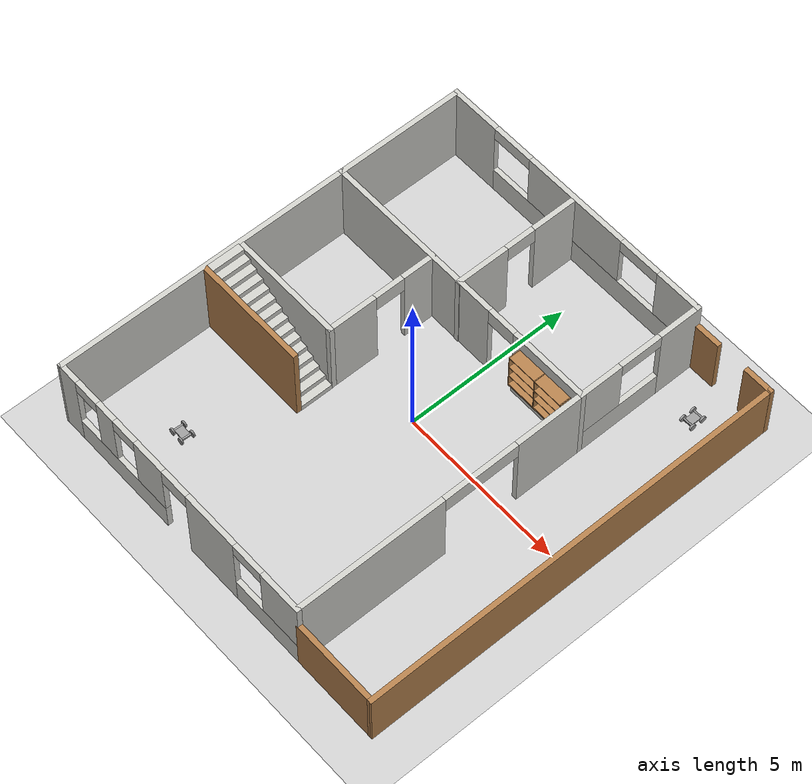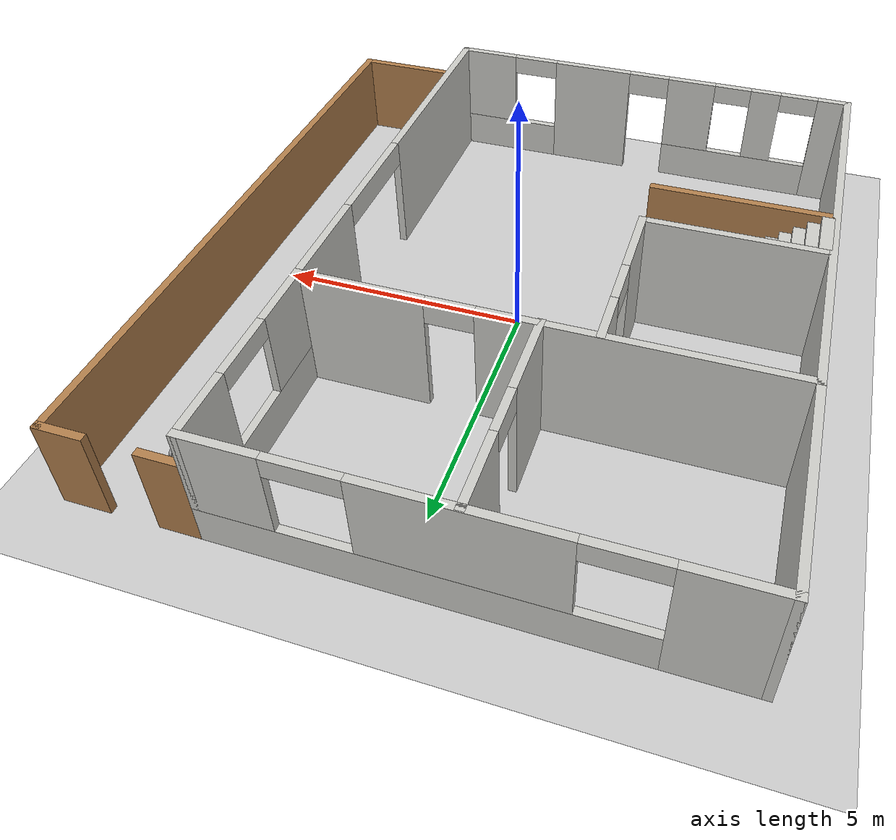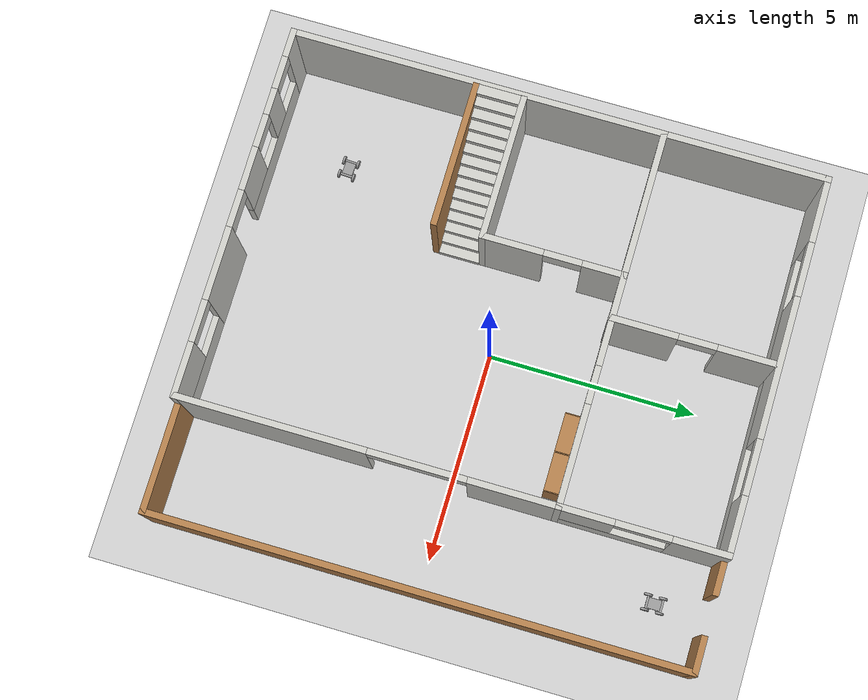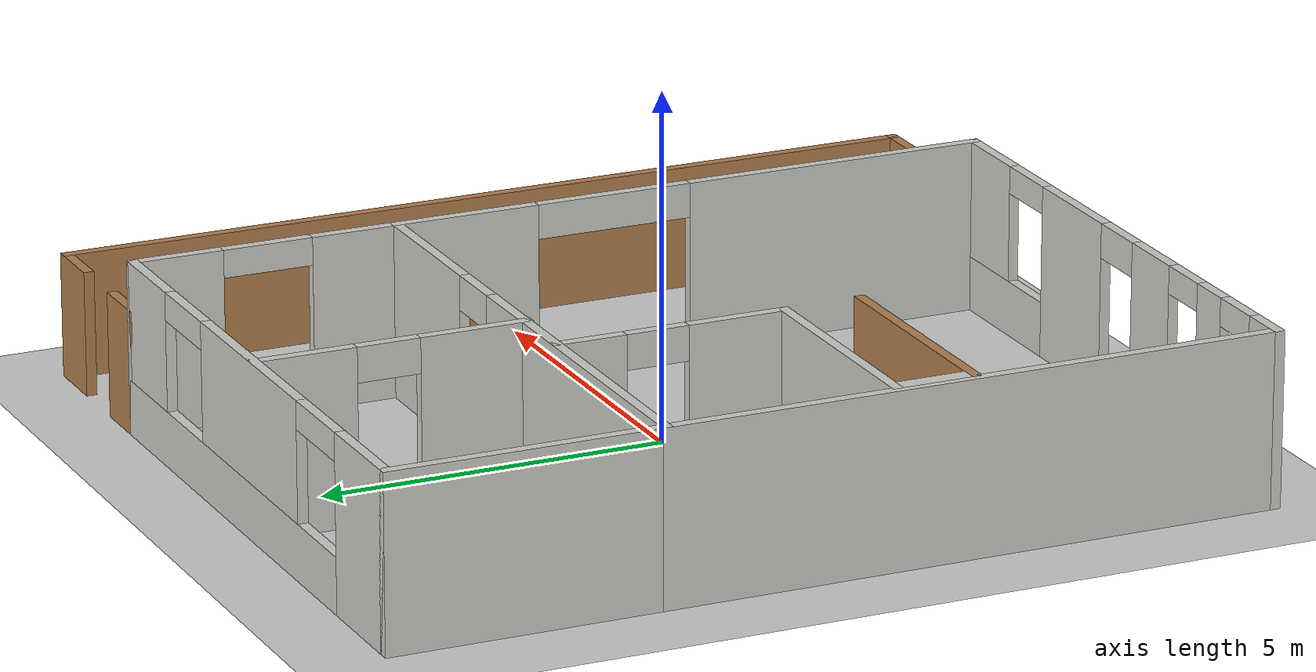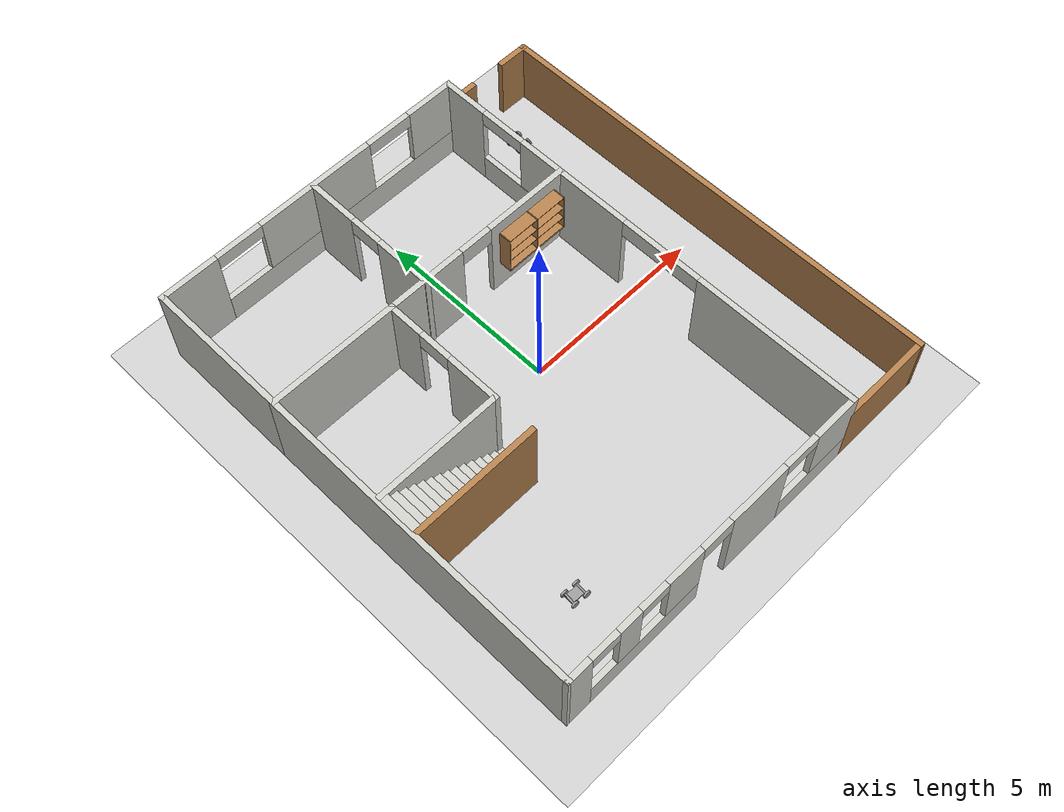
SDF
<sdf version="1.7">
 <world name="default">
  <plugin name="hello" filename="libhello.so"/>
  <light name="sun" type="directional">
   <pose>0 0 10 0 -0 0</pose>
   <diffuse>0.8 0.8 0.8 1</diffuse>
   <specular>0.2 0.2 0.2 1</specular>
   <attenuation>
    <range>1000</range>
    <constant>0.9</constant>
    <linear>0.01</linear>
    <quadratic>0.001</quadratic>
   </attenuation>
   <direction>-0.5 0.1 -0.9</direction>
   <spot><inner_angle>0</inner_angle><outer_angle>0</outer_angle><falloff>0</falloff></spot>
  </light>
  <model name="ground_plane">
   <static>1</static>
   <link name="link">
    <collision name="collision">
     <geometry><plane><normal>0 0 1</normal><size>100 100</size></plane></geometry>
     <surface>
      <contact><collide_bitmask>65535</collide_bitmask></contact>
      <friction><ode><mu>100</mu><mu2>50</mu2></ode></friction>
     </surface>
    </collision>
    <visual name="visual">
     <cast_shadows>0</cast_shadows>
     <geometry><plane><normal>0 0 1</normal><size>100 100</size></plane></geometry>
     <material>
      <script><uri>file://media/materials/scripts/gazebo.material</uri><name>Gazebo/Grey</name></script>
     </material>
    </visual>
   </link>
  </model>
  <gravity>0 0 -9.8</gravity>
  <magnetic_field>6e-06 2.3e-05 -4.2e-05</magnetic_field>
  <atmosphere type="adiabatic"/>
  <physics type="ode">
   <max_step_size>0.001</max_step_size>
   <real_time_factor>1</real_time_factor>
   <real_time_update_rate>1000</real_time_update_rate>
  </physics>
  <scene><ambient>0.4 0.4 0.4 1</ambient><background>0.7 0.7 0.7 1</background><shadows>1</shadows></scene>
  <audio><device>default</device></audio>
  <spherical_coordinates>
   <surface_model>EARTH_WGS84</surface_model>
   <latitude_deg>0</latitude_deg>
   <longitude_deg>0</longitude_deg>
   <elevation>0</elevation>
   <heading_deg>0</heading_deg>
  </spherical_coordinates>
  <model name="house">
   <link name="Stairs_0">
    <inertial>
     <mass>1</mass>
     <inertia><ixx>1</ixx><ixy>0</ixy><ixz>0</ixz><iyy>1</iyy><iyz>0</iyz><izz>1</izz></inertia>
    </inertial>
    <visual name="Stairs_0_Visual_12">
     <pose>-5.11434 -1.37452 2.08333 0 0 -1.5708</pose>
     <geometry><box><size>1 0.233333 0.166667</size></box></geometry>
     <material>
      <script><uri>file://media/materials/scripts/gazebo.material</uri><name>Gazebo/CeilingTiled</name></script>
      <ambient>1 1 1 1</ambient>
      <shader type="pixel"><normal_map>__default__</normal_map></shader>
     </material>
     <meta><layer>0</layer></meta>
    </visual>
    <visual name="Stairs_0_Visual_6">
     <pose>-3.71434 -1.37452 1.08333 0 0 -1.5708</pose>
     <geometry><box><size>1 0.233333 0.166667</size></box></geometry>
     <material>
      <script><uri>file://media/materials/scripts/gazebo.material</uri><name>Gazebo/CeilingTiled</name></script>
      <ambient>1 1 1 1</ambient>
      <shader type="pixel"><normal_map>__default__</normal_map></shader>
     </material>
     <meta><layer>0</layer></meta>
    </visual>
    <visual name="Stairs_0_Visual_13">
     <pose>-5.34767 -1.37452 2.25 0 0 -1.5708</pose>
     <geometry><box><size>1 0.233333 0.166667</size></box></geometry>
     <material>
      <script><uri>file://media/materials/scripts/gazebo.material</uri><name>Gazebo/CeilingTiled</name></script>
      <ambient>1 1 1 1</ambient>
      <shader type="pixel"><normal_map>__default__</normal_map></shader>
     </material>
     <meta><layer>0</layer></meta>
    </visual>
    <visual name="Stairs_0_Visual_9">
     <pose>-4.41434 -1.37452 1.58333 0 0 -1.5708</pose>
     <geometry><box><size>1 0.233333 0.166667</size></box></geometry>
     <material>
      <script><uri>file://media/materials/scripts/gazebo.material</uri><name>Gazebo/CeilingTiled</name></script>
      <ambient>1 1 1 1</ambient>
      <shader type="pixel"><normal_map>__default__</normal_map></shader>
     </material>
     <meta><layer>0</layer></meta>
    </visual>
    <visual name="Stairs_0_Visual_7">
     <pose>-3.94767 -1.37452 1.25 0 0 -1.5708</pose>
     <geometry><box><size>1 0.233333 0.166667</size></box></geometry>
     <material>
      <script><uri>file://media/materials/scripts/gazebo.material</uri><name>Gazebo/CeilingTiled</name></script>
      <ambient>1 1 1 1</ambient>
      <shader type="pixel"><normal_map>__default__</normal_map></shader>
     </material>
     <meta><layer>0</layer></meta>
    </visual>
    <visual name="Stairs_0_Visual_0">
     <pose>-2.31434 -1.37452 0.083333 0 0 -1.5708</pose>
     <geometry><box><size>1 0.233333 0.166667</size></box></geometry>
     <material>
      <script><uri>file://media/materials/scripts/gazebo.material</uri><name>Gazebo/CeilingTiled</name></script>
      <ambient>1 1 1 1</ambient>
      <shader type="pixel"><normal_map>__default__</normal_map></shader>
     </material>
     <meta><layer>0</layer></meta>
    </visual>
    <visual name="Stairs_0_Visual_3">
     <pose>-3.01434 -1.37452 0.583333 0 0 -1.5708</pose>
     <geometry><box><size>1 0.233333 0.166667</size></box></geometry>
     <material>
      <script><uri>file://media/materials/scripts/gazebo.material</uri><name>Gazebo/CeilingTiled</name></script>
      <ambient>1 1 1 1</ambient>
      <shader type="pixel"><normal_map>__default__</normal_map></shader>
     </material>
     <meta><layer>0</layer></meta>
    </visual>
    <visual name="Stairs_0_Visual_4">
     <pose>-3.24767 -1.37452 0.75 0 0 -1.5708</pose>
     <geometry><box><size>1 0.233333 0.166667</size></box></geometry>
     <material>
      <script><uri>file://media/materials/scripts/gazebo.material</uri><name>Gazebo/CeilingTiled</name></script>
      <ambient>1 1 1 1</ambient>
      <shader type="pixel"><normal_map>__default__</normal_map></shader>
     </material>
     <meta><layer>0</layer></meta>
    </visual>
    <visual name="Stairs_0_Visual_1">
     <pose>-2.54767 -1.37452 0.25 0 0 -1.5708</pose>
     <geometry><box><size>1 0.233333 0.166667</size></box></geometry>
     <material>
      <script><uri>file://media/materials/scripts/gazebo.material</uri><name>Gazebo/CeilingTiled</name></script>
      <ambient>1 1 1 1</ambient>
      <shader type="pixel"><normal_map>__default__</normal_map></shader>
     </material>
     <meta><layer>0</layer></meta>
    </visual>
    <visual name="Stairs_0_Visual_11">
     <pose>-4.88101 -1.37452 1.91667 0 0 -1.5708</pose>
     <geometry><box><size>1 0.233333 0.166667</size></box></geometry>
     <material>
      <script><uri>file://media/materials/scripts/gazebo.material</uri><name>Gazebo/CeilingTiled</name></script>
      <ambient>1 1 1 1</ambient>
      <shader type="pixel"><normal_map>__default__</normal_map></shader>
     </material>
     <meta><layer>0</layer></meta>
    </visual>
    <visual name="Stairs_0_Visual_10">
     <pose>-4.64767 -1.37452 1.75 0 0 -1.5708</pose>
     <geometry><box><size>1 0.233333 0.166667</size></box></geometry>
     <material>
      <script><uri>file://media/materials/scripts/gazebo.material</uri><name>Gazebo/CeilingTiled</name></script>
      <ambient>1 1 1 1</ambient>
      <shader type="pixel"><normal_map>__default__</normal_map></shader>
     </material>
     <meta><layer>0</layer></meta>
    </visual>
    <visual name="Stairs_0_Visual_14">
     <pose>-5.58101 -1.37452 2.41667 0 0 -1.5708</pose>
     <geometry><box><size>1 0.233333 0.166667</size></box></geometry>
     <material>
      <script><uri>file://media/materials/scripts/gazebo.material</uri><name>Gazebo/CeilingTiled</name></script>
      <ambient>1 1 1 1</ambient>
      <shader type="pixel"><normal_map>__default__</normal_map></shader>
     </material>
     <meta><layer>0</layer></meta>
    </visual>
    <visual name="Stairs_0_Visual_5">
     <pose>-3.48101 -1.37452 0.916667 0 0 -1.5708</pose>
     <geometry><box><size>1 0.233333 0.166667</size></box></geometry>
     <material>
      <script><uri>file://media/materials/scripts/gazebo.material</uri><name>Gazebo/CeilingTiled</name></script>
      <ambient>1 1 1 1</ambient>
      <shader type="pixel"><normal_map>__default__</normal_map></shader>
     </material>
     <meta><layer>0</layer></meta>
    </visual>
    <visual name="Stairs_0_Visual_8">
     <pose>-4.181 -1.37452 1.41667 0 0 -1.5708</pose>
     <geometry><box><size>1 0.233333 0.166667</size></box></geometry>
     <material>
      <script><uri>file://media/materials/scripts/gazebo.material</uri><name>Gazebo/CeilingTiled</name></script>
      <ambient>1 1 1 1</ambient>
      <shader type="pixel"><normal_map>__default__</normal_map></shader>
     </material>
     <meta><layer>0</layer></meta>
    </visual>
    <visual name="Stairs_0_Visual_2">
     <pose>-2.781 -1.37452 0.416667 0 0 -1.5708</pose>
     <geometry><box><size>1 0.233333 0.166667</size></box></geometry>
     <material>
      <script><uri>file://media/materials/scripts/gazebo.material</uri><name>Gazebo/CeilingTiled</name></script>
      <ambient>1 1 1 1</ambient>
      <shader type="pixel"><normal_map>__default__</normal_map></shader>
     </material>
     <meta><layer>0</layer></meta>
    </visual>
    <collision name="Stairs_0_Collision_5">
     <pose>-3.48101 -1.37452 0.916667 0 0 -1.5708</pose>
     <geometry><box><size>1 0.233333 0.166667</size></box></geometry>
     <surface>
      <friction>
       <ode><mu>1</mu><mu2>1</mu2><fdir1>0 0 0</fdir1><slip1>0</slip1><slip2>0</slip2></ode>
       <torsional>
        <coefficient>1</coefficient>
        <patch_radius>0</patch_radius>
        <surface_radius>0</surface_radius>
        <use_patch_radius>1</use_patch_radius>
        <ode><slip>0</slip></ode>
       </torsional>
      </friction>
      <bounce><restitution_coefficient>0</restitution_coefficient><threshold>1e+06</threshold></bounce>
      <contact>
       <collide_without_contact>0</collide_without_contact>
       <collide_without_contact_bitmask>1</collide_without_contact_bitmask>
       <collide_bitmask>1</collide_bitmask>
       <ode>
        <soft_cfm>0</soft_cfm>
        <soft_erp>0.2</soft_erp>
        <kp>1e+13</kp>
        <kd>1</kd>
        <max_vel>0.01</max_vel>
        <min_depth>0</min_depth>
       </ode>
       <bullet>
        <split_impulse>1</split_impulse>
        <split_impulse_penetration_threshold>-0.01</split_impulse_penetration_threshold>
        <soft_cfm>0</soft_cfm>
        <soft_erp>0.2</soft_erp>
        <kp>1e+13</kp>
        <kd>1</kd>
       </bullet>
      </contact>
     </surface>
    </collision>
    <collision name="Stairs_0_Collision_3">
     <pose>-3.01434 -1.37452 0.583333 0 0 -1.5708</pose>
     <geometry><box><size>1 0.233333 0.166667</size></box></geometry>
     <surface>
      <friction>
       <ode><mu>1</mu><mu2>1</mu2><fdir1>0 0 0</fdir1><slip1>0</slip1><slip2>0</slip2></ode>
       <torsional>
        <coefficient>1</coefficient>
        <patch_radius>0</patch_radius>
        <surface_radius>0</surface_radius>
        <use_patch_radius>1</use_patch_radius>
        <ode><slip>0</slip></ode>
       </torsional>
      </friction>
      <bounce><restitution_coefficient>0</restitution_coefficient><threshold>1e+06</threshold></bounce>
      <contact>
       <collide_without_contact>0</collide_without_contact>
       <collide_without_contact_bitmask>1</collide_without_contact_bitmask>
       <collide_bitmask>1</collide_bitmask>
       <ode>
        <soft_cfm>0</soft_cfm>
        <soft_erp>0.2</soft_erp>
        <kp>1e+13</kp>
        <kd>1</kd>
        <max_vel>0.01</max_vel>
        <min_depth>0</min_depth>
       </ode>
       <bullet>
        <split_impulse>1</split_impulse>
        <split_impulse_penetration_threshold>-0.01</split_impulse_penetration_threshold>
        <soft_cfm>0</soft_cfm>
        <soft_erp>0.2</soft_erp>
        <kp>1e+13</kp>
        <kd>1</kd>
       </bullet>
      </contact>
     </surface>
    </collision>
    <collision name="Stairs_0_Collision_4">
     <pose>-3.24767 -1.37452 0.75 0 0 -1.5708</pose>
     <geometry><box><size>1 0.233333 0.166667</size></box></geometry>
     <surface>
      <friction>
       <ode><mu>1</mu><mu2>1</mu2><fdir1>0 0 0</fdir1><slip1>0</slip1><slip2>0</slip2></ode>
       <torsional>
        <coefficient>1</coefficient>
        <patch_radius>0</patch_radius>
        <surface_radius>0</surface_radius>
        <use_patch_radius>1</use_patch_radius>
        <ode><slip>0</slip></ode>
       </torsional>
      </friction>
      <bounce><restitution_coefficient>0</restitution_coefficient><threshold>1e+06</threshold></bounce>
      <contact>
       <collide_without_contact>0</collide_without_contact>
       <collide_without_contact_bitmask>1</collide_without_contact_bitmask>
       <collide_bitmask>1</collide_bitmask>
       <ode>
        <soft_cfm>0</soft_cfm>
        <soft_erp>0.2</soft_erp>
        <kp>1e+13</kp>
        <kd>1</kd>
        <max_vel>0.01</max_vel>
        <min_depth>0</min_depth>
       </ode>
       <bullet>
        <split_impulse>1</split_impulse>
        <split_impulse_penetration_threshold>-0.01</split_impulse_penetration_threshold>
        <soft_cfm>0</soft_cfm>
        <soft_erp>0.2</soft_erp>
        <kp>1e+13</kp>
        <kd>1</kd>
       </bullet>
      </contact>
     </surface>
    </collision>
    <collision name="Stairs_0_Collision_8">
     <pose>-4.181 -1.37452 1.41667 0 0 -1.5708</pose>
     <geometry><box><size>1 0.233333 0.166667</size></box></geometry>
     <surface>
      <friction>
       <ode><mu>1</mu><mu2>1</mu2><fdir1>0 0 0</fdir1><slip1>0</slip1><slip2>0</slip2></ode>
       <torsional>
        <coefficient>1</coefficient>
        <patch_radius>0</patch_radius>
        <surface_radius>0</surface_radius>
        <use_patch_radius>1</use_patch_radius>
        <ode><slip>0</slip></ode>
       </torsional>
      </friction>
      <bounce><restitution_coefficient>0</restitution_coefficient><threshold>1e+06</threshold></bounce>
      <contact>
       <collide_without_contact>0</collide_without_contact>
       <collide_without_contact_bitmask>1</collide_without_contact_bitmask>
       <collide_bitmask>1</collide_bitmask>
       <ode>
        <soft_cfm>0</soft_cfm>
        <soft_erp>0.2</soft_erp>
        <kp>1e+13</kp>
        <kd>1</kd>
        <max_vel>0.01</max_vel>
        <min_depth>0</min_depth>
       </ode>
       <bullet>
        <split_impulse>1</split_impulse>
        <split_impulse_penetration_threshold>-0.01</split_impulse_penetration_threshold>
        <soft_cfm>0</soft_cfm>
        <soft_erp>0.2</soft_erp>
        <kp>1e+13</kp>
        <kd>1</kd>
       </bullet>
      </contact>
     </surface>
    </collision>
    <collision name="Stairs_0_Collision_14">
     <pose>-5.58101 -1.37452 2.41667 0 0 -1.5708</pose>
     <geometry><box><size>1 0.233333 0.166667</size></box></geometry>
     <surface>
      <friction>
       <ode><mu>1</mu><mu2>1</mu2><fdir1>0 0 0</fdir1><slip1>0</slip1><slip2>0</slip2></ode>
       <torsional>
        <coefficient>1</coefficient>
        <patch_radius>0</patch_radius>
        <surface_radius>0</surface_radius>
        <use_patch_radius>1</use_patch_radius>
        <ode><slip>0</slip></ode>
       </torsional>
      </friction>
      <bounce><restitution_coefficient>0</restitution_coefficient><threshold>1e+06</threshold></bounce>
      <contact>
       <collide_without_contact>0</collide_without_contact>
       <collide_without_contact_bitmask>1</collide_without_contact_bitmask>
       <collide_bitmask>1</collide_bitmask>
       <ode>
        <soft_cfm>0</soft_cfm>
        <soft_erp>0.2</soft_erp>
        <kp>1e+13</kp>
        <kd>1</kd>
        <max_vel>0.01</max_vel>
        <min_depth>0</min_depth>
       </ode>
       <bullet>
        <split_impulse>1</split_impulse>
        <split_impulse_penetration_threshold>-0.01</split_impulse_penetration_threshold>
        <soft_cfm>0</soft_cfm>
        <soft_erp>0.2</soft_erp>
        <kp>1e+13</kp>
        <kd>1</kd>
       </bullet>
      </contact>
     </surface>
    </collision>
    <collision name="Stairs_0_Collision_12">
     <pose>-5.11434 -1.37452 2.08333 0 0 -1.5708</pose>
     <geometry><box><size>1 0.233333 0.166667</size></box></geometry>
     <surface>
      <friction>
       <ode><mu>1</mu><mu2>1</mu2><fdir1>0 0 0</fdir1><slip1>0</slip1><slip2>0</slip2></ode>
       <torsional>
        <coefficient>1</coefficient>
        <patch_radius>0</patch_radius>
        <surface_radius>0</surface_radius>
        <use_patch_radius>1</use_patch_radius>
        <ode><slip>0</slip></ode>
       </torsional>
      </friction>
      <bounce><restitution_coefficient>0</restitution_coefficient><threshold>1e+06</threshold></bounce>
      <contact>
       <collide_without_contact>0</collide_without_contact>
       <collide_without_contact_bitmask>1</collide_without_contact_bitmask>
       <collide_bitmask>1</collide_bitmask>
       <ode>
        <soft_cfm>0</soft_cfm>
        <soft_erp>0.2</soft_erp>
        <kp>1e+13</kp>
        <kd>1</kd>
        <max_vel>0.01</max_vel>
        <min_depth>0</min_depth>
       </ode>
       <bullet>
        <split_impulse>1</split_impulse>
        <split_impulse_penetration_threshold>-0.01</split_impulse_penetration_threshold>
        <soft_cfm>0</soft_cfm>
        <soft_erp>0.2</soft_erp>
        <kp>1e+13</kp>
        <kd>1</kd>
       </bullet>
      </contact>
     </surface>
    </collision>
    <collision name="Stairs_0_Collision_2">
     <pose>-2.781 -1.37452 0.416667 0 0 -1.5708</pose>
     <geometry><box><size>1 0.233333 0.166667</size></box></geometry>
     <surface>
      <friction>
       <ode><mu>1</mu><mu2>1</mu2><fdir1>0 0 0</fdir1><slip1>0</slip1><slip2>0</slip2></ode>
       <torsional>
        <coefficient>1</coefficient>
        <patch_radius>0</patch_radius>
        <surface_radius>0</surface_radius>
        <use_patch_radius>1</use_patch_radius>
        <ode><slip>0</slip></ode>
       </torsional>
      </friction>
      <bounce><restitution_coefficient>0</restitution_coefficient><threshold>1e+06</threshold></bounce>
      <contact>
       <collide_without_contact>0</collide_without_contact>
       <collide_without_contact_bitmask>1</collide_without_contact_bitmask>
       <collide_bitmask>1</collide_bitmask>
       <ode>
        <soft_cfm>0</soft_cfm>
        <soft_erp>0.2</soft_erp>
        <kp>1e+13</kp>
        <kd>1</kd>
        <max_vel>0.01</max_vel>
        <min_depth>0</min_depth>
       </ode>
       <bullet>
        <split_impulse>1</split_impulse>
        <split_impulse_penetration_threshold>-0.01</split_impulse_penetration_threshold>
        <soft_cfm>0</soft_cfm>
        <soft_erp>0.2</soft_erp>
        <kp>1e+13</kp>
        <kd>1</kd>
       </bullet>
      </contact>
     </surface>
    </collision>
    <collision name="Stairs_0_Collision_9">
     <pose>-4.41434 -1.37452 1.58333 0 0 -1.5708</pose>
     <geometry><box><size>1 0.233333 0.166667</size></box></geometry>
     <surface>
      <friction>
       <ode><mu>1</mu><mu2>1</mu2><fdir1>0 0 0</fdir1><slip1>0</slip1><slip2>0</slip2></ode>
       <torsional>
        <coefficient>1</coefficient>
        <patch_radius>0</patch_radius>
        <surface_radius>0</surface_radius>
        <use_patch_radius>1</use_patch_radius>
        <ode><slip>0</slip></ode>
       </torsional>
      </friction>
      <bounce><restitution_coefficient>0</restitution_coefficient><threshold>1e+06</threshold></bounce>
      <contact>
       <collide_without_contact>0</collide_without_contact>
       <collide_without_contact_bitmask>1</collide_without_contact_bitmask>
       <collide_bitmask>1</collide_bitmask>
       <ode>
        <soft_cfm>0</soft_cfm>
        <soft_erp>0.2</soft_erp>
        <kp>1e+13</kp>
        <kd>1</kd>
        <max_vel>0.01</max_vel>
        <min_depth>0</min_depth>
       </ode>
       <bullet>
        <split_impulse>1</split_impulse>
        <split_impulse_penetration_threshold>-0.01</split_impulse_penetration_threshold>
        <soft_cfm>0</soft_cfm>
        <soft_erp>0.2</soft_erp>
        <kp>1e+13</kp>
        <kd>1</kd>
       </bullet>
      </contact>
     </surface>
    </collision>
    <collision name="Stairs_0_Collision_6">
     <pose>-3.71434 -1.37452 1.08333 0 0 -1.5708</pose>
     <geometry><box><size>1 0.233333 0.166667</size></box></geometry>
     <surface>
      <friction>
       <ode><mu>1</mu><mu2>1</mu2><fdir1>0 0 0</fdir1><slip1>0</slip1><slip2>0</slip2></ode>
       <torsional>
        <coefficient>1</coefficient>
        <patch_radius>0</patch_radius>
        <surface_radius>0</surface_radius>
        <use_patch_radius>1</use_patch_radius>
        <ode><slip>0</slip></ode>
       </torsional>
      </friction>
      <bounce><restitution_coefficient>0</restitution_coefficient><threshold>1e+06</threshold></bounce>
      <contact>
       <collide_without_contact>0</collide_without_contact>
       <collide_without_contact_bitmask>1</collide_without_contact_bitmask>
       <collide_bitmask>1</collide_bitmask>
       <ode>
        <soft_cfm>0</soft_cfm>
        <soft_erp>0.2</soft_erp>
        <kp>1e+13</kp>
        <kd>1</kd>
        <max_vel>0.01</max_vel>
        <min_depth>0</min_depth>
       </ode>
       <bullet>
        <split_impulse>1</split_impulse>
        <split_impulse_penetration_threshold>-0.01</split_impulse_penetration_threshold>
        <soft_cfm>0</soft_cfm>
        <soft_erp>0.2</soft_erp>
        <kp>1e+13</kp>
        <kd>1</kd>
       </bullet>
      </contact>
     </surface>
    </collision>
    <collision name="Stairs_0_Collision_13">
     <pose>-5.34767 -1.37452 2.25 0 0 -1.5708</pose>
     <geometry><box><size>1 0.233333 0.166667</size></box></geometry>
     <surface>
      <friction>
       <ode><mu>1</mu><mu2>1</mu2><fdir1>0 0 0</fdir1><slip1>0</slip1><slip2>0</slip2></ode>
       <torsional>
        <coefficient>1</coefficient>
        <patch_radius>0</patch_radius>
        <surface_radius>0</surface_radius>
        <use_patch_radius>1</use_patch_radius>
        <ode><slip>0</slip></ode>
       </torsional>
      </friction>
      <bounce><restitution_coefficient>0</restitution_coefficient><threshold>1e+06</threshold></bounce>
      <contact>
       <collide_without_contact>0</collide_without_contact>
       <collide_without_contact_bitmask>1</collide_without_contact_bitmask>
       <collide_bitmask>1</collide_bitmask>
       <ode>
        <soft_cfm>0</soft_cfm>
        <soft_erp>0.2</soft_erp>
        <kp>1e+13</kp>
        <kd>1</kd>
        <max_vel>0.01</max_vel>
        <min_depth>0</min_depth>
       </ode>
       <bullet>
        <split_impulse>1</split_impulse>
        <split_impulse_penetration_threshold>-0.01</split_impulse_penetration_threshold>
        <soft_cfm>0</soft_cfm>
        <soft_erp>0.2</soft_erp>
        <kp>1e+13</kp>
        <kd>1</kd>
       </bullet>
      </contact>
     </surface>
    </collision>
    <collision name="Stairs_0_Collision_7">
     <pose>-3.94767 -1.37452 1.25 0 0 -1.5708</pose>
     <geometry><box><size>1 0.233333 0.166667</size></box></geometry>
     <surface>
      <friction>
       <ode><mu>1</mu><mu2>1</mu2><fdir1>0 0 0</fdir1><slip1>0</slip1><slip2>0</slip2></ode>
       <torsional>
        <coefficient>1</coefficient>
        <patch_radius>0</patch_radius>
        <surface_radius>0</surface_radius>
        <use_patch_radius>1</use_patch_radius>
        <ode><slip>0</slip></ode>
       </torsional>
      </friction>
      <bounce><restitution_coefficient>0</restitution_coefficient><threshold>1e+06</threshold></bounce>
      <contact>
       <collide_without_contact>0</collide_without_contact>
       <collide_without_contact_bitmask>1</collide_without_contact_bitmask>
       <collide_bitmask>1</collide_bitmask>
       <ode>
        <soft_cfm>0</soft_cfm>
        <soft_erp>0.2</soft_erp>
        <kp>1e+13</kp>
        <kd>1</kd>
        <max_vel>0.01</max_vel>
        <min_depth>0</min_depth>
       </ode>
       <bullet>
        <split_impulse>1</split_impulse>
        <split_impulse_penetration_threshold>-0.01</split_impulse_penetration_threshold>
        <soft_cfm>0</soft_cfm>
        <soft_erp>0.2</soft_erp>
        <kp>1e+13</kp>
        <kd>1</kd>
       </bullet>
      </contact>
     </surface>
    </collision>
    <collision name="Stairs_0_Collision_0">
     <pose>-2.31434 -1.37452 0.083333 0 0 -1.5708</pose>
     <geometry><box><size>1 0.233333 0.166667</size></box></geometry>
     <surface>
      <friction>
       <ode><mu>1</mu><mu2>1</mu2><fdir1>0 0 0</fdir1><slip1>0</slip1><slip2>0</slip2></ode>
       <torsional>
        <coefficient>1</coefficient>
        <patch_radius>0</patch_radius>
        <surface_radius>0</surface_radius>
        <use_patch_radius>1</use_patch_radius>
        <ode><slip>0</slip></ode>
       </torsional>
      </friction>
      <bounce><restitution_coefficient>0</restitution_coefficient><threshold>1e+06</threshold></bounce>
      <contact>
       <collide_without_contact>0</collide_without_contact>
       <collide_without_contact_bitmask>1</collide_without_contact_bitmask>
       <collide_bitmask>1</collide_bitmask>
       <ode>
        <soft_cfm>0</soft_cfm>
        <soft_erp>0.2</soft_erp>
        <kp>1e+13</kp>
        <kd>1</kd>
        <max_vel>0.01</max_vel>
        <min_depth>0</min_depth>
       </ode>
       <bullet>
        <split_impulse>1</split_impulse>
        <split_impulse_penetration_threshold>-0.01</split_impulse_penetration_threshold>
        <soft_cfm>0</soft_cfm>
        <soft_erp>0.2</soft_erp>
        <kp>1e+13</kp>
        <kd>1</kd>
       </bullet>
      </contact>
     </surface>
    </collision>
    <collision name="Stairs_0_Collision_11">
     <pose>-4.88101 -1.37452 1.91667 0 0 -1.5708</pose>
     <geometry><box><size>1 0.233333 0.166667</size></box></geometry>
     <surface>
      <friction>
       <ode><mu>1</mu><mu2>1</mu2><fdir1>0 0 0</fdir1><slip1>0</slip1><slip2>0</slip2></ode>
       <torsional>
        <coefficient>1</coefficient>
        <patch_radius>0</patch_radius>
        <surface_radius>0</surface_radius>
        <use_patch_radius>1</use_patch_radius>
        <ode><slip>0</slip></ode>
       </torsional>
      </friction>
      <bounce><restitution_coefficient>0</restitution_coefficient><threshold>1e+06</threshold></bounce>
      <contact>
       <collide_without_contact>0</collide_without_contact>
       <collide_without_contact_bitmask>1</collide_without_contact_bitmask>
       <collide_bitmask>1</collide_bitmask>
       <ode>
        <soft_cfm>0</soft_cfm>
        <soft_erp>0.2</soft_erp>
        <kp>1e+13</kp>
        <kd>1</kd>
        <max_vel>0.01</max_vel>
        <min_depth>0</min_depth>
       </ode>
       <bullet>
        <split_impulse>1</split_impulse>
        <split_impulse_penetration_threshold>-0.01</split_impulse_penetration_threshold>
        <soft_cfm>0</soft_cfm>
        <soft_erp>0.2</soft_erp>
        <kp>1e+13</kp>
        <kd>1</kd>
       </bullet>
      </contact>
     </surface>
    </collision>
    <collision name="Stairs_0_Collision_1">
     <pose>-2.54767 -1.37452 0.25 0 0 -1.5708</pose>
     <geometry><box><size>1 0.233333 0.166667</size></box></geometry>
     <surface>
      <friction>
       <ode><mu>1</mu><mu2>1</mu2><fdir1>0 0 0</fdir1><slip1>0</slip1><slip2>0</slip2></ode>
       <torsional>
        <coefficient>1</coefficient>
        <patch_radius>0</patch_radius>
        <surface_radius>0</surface_radius>
        <use_patch_radius>1</use_patch_radius>
        <ode><slip>0</slip></ode>
       </torsional>
      </friction>
      <bounce><restitution_coefficient>0</restitution_coefficient><threshold>1e+06</threshold></bounce>
      <contact>
       <collide_without_contact>0</collide_without_contact>
       <collide_without_contact_bitmask>1</collide_without_contact_bitmask>
       <collide_bitmask>1</collide_bitmask>
       <ode>
        <soft_cfm>0</soft_cfm>
        <soft_erp>0.2</soft_erp>
        <kp>1e+13</kp>
        <kd>1</kd>
        <max_vel>0.01</max_vel>
        <min_depth>0</min_depth>
       </ode>
       <bullet>
        <split_impulse>1</split_impulse>
        <split_impulse_penetration_threshold>-0.01</split_impulse_penetration_threshold>
        <soft_cfm>0</soft_cfm>
        <soft_erp>0.2</soft_erp>
        <kp>1e+13</kp>
        <kd>1</kd>
       </bullet>
      </contact>
     </surface>
    </collision>
    <collision name="Stairs_0_Collision_10">
     <pose>-4.64767 -1.37452 1.75 0 0 -1.5708</pose>
     <geometry><box><size>1 0.233333 0.166667</size></box></geometry>
     <surface>
      <friction>
       <ode><mu>1</mu><mu2>1</mu2><fdir1>0 0 0</fdir1><slip1>0</slip1><slip2>0</slip2></ode>
       <torsional>
        <coefficient>1</coefficient>
        <patch_radius>0</patch_radius>
        <surface_radius>0</surface_radius>
        <use_patch_radius>1</use_patch_radius>
        <ode><slip>0</slip></ode>
       </torsional>
      </friction>
      <bounce><restitution_coefficient>0</restitution_coefficient><threshold>1e+06</threshold></bounce>
      <contact>
       <collide_without_contact>0</collide_without_contact>
       <collide_without_contact_bitmask>1</collide_without_contact_bitmask>
       <collide_bitmask>1</collide_bitmask>
       <ode>
        <soft_cfm>0</soft_cfm>
        <soft_erp>0.2</soft_erp>
        <kp>1e+13</kp>
        <kd>1</kd>
        <max_vel>0.01</max_vel>
        <min_depth>0</min_depth>
       </ode>
       <bullet>
        <split_impulse>1</split_impulse>
        <split_impulse_penetration_threshold>-0.01</split_impulse_penetration_threshold>
        <soft_cfm>0</soft_cfm>
        <soft_erp>0.2</soft_erp>
        <kp>1e+13</kp>
        <kd>1</kd>
       </bullet>
      </contact>
     </surface>
    </collision>
   </link>
   <link name="Wall_0">
    <pose>-5.72496 -1.92194 0 0 -0 1.5708</pose>
    <visual name="Wall_0_Visual">
     <pose>0 0 1.25 0 -0 0</pose>
     <geometry><box><size>9 0.15 2.5</size></box></geometry>
     <material>
      <script><uri>file://media/materials/scripts/gazebo.material</uri><name>Gazebo/CeilingTiled</name></script>
      <ambient>1 1 1 1</ambient>
      <shader type="pixel"/>
     </material>
     <meta><layer>0</layer></meta>
    </visual>
    <collision name="Wall_0_Collision">
     <pose>0 0 1.25 0 -0 0</pose>
     <geometry><box><size>9 0.15 2.5</size></box></geometry>
     <surface>
      <friction>
       <ode><mu>1</mu><mu2>1</mu2><fdir1>0 0 0</fdir1><slip1>0</slip1><slip2>0</slip2></ode>
       <torsional>
        <coefficient>1</coefficient>
        <patch_radius>0</patch_radius>
        <surface_radius>0</surface_radius>
        <use_patch_radius>1</use_patch_radius>
        <ode><slip>0</slip></ode>
       </torsional>
      </friction>
      <bounce><restitution_coefficient>0</restitution_coefficient><threshold>1e+06</threshold></bounce>
      <contact>
       <collide_without_contact>0</collide_without_contact>
       <collide_without_contact_bitmask>1</collide_without_contact_bitmask>
       <collide_bitmask>1</collide_bitmask>
       <ode>
        <soft_cfm>0</soft_cfm>
        <soft_erp>0.2</soft_erp>
        <kp>1e+13</kp>
        <kd>1</kd>
        <max_vel>0.01</max_vel>
        <min_depth>0</min_depth>
       </ode>
       <bullet>
        <split_impulse>1</split_impulse>
        <split_impulse_penetration_threshold>-0.01</split_impulse_penetration_threshold>
        <soft_cfm>0</soft_cfm>
        <soft_erp>0.2</soft_erp>
        <kp>1e+13</kp>
        <kd>1</kd>
       </bullet>
      </contact>
     </surface>
    </collision>
   </link>
   <link name="Wall_13">
    <pose>-2.28096 0.843058 0 0 -0 1.5708</pose>
    <visual name="Wall_13_Visual_2">
     <pose>0.228595 0 2.25 0 -0 0</pose>
     <geometry><box><size>0.9 0.15 0.5</size></box></geometry>
     <material>
      <script><uri>file://media/materials/scripts/gazebo.material</uri><name>Gazebo/CeilingTiled</name></script>
      <ambient>1 1 1 1</ambient>
      <shader type="pixel"/>
     </material>
     <meta><layer>0</layer></meta>
    </visual>
    <visual name="Wall_13_Visual_1">
     <pose>1.2018 0 1.25 0 -0 0</pose>
     <geometry><box><size>1.04641 0.15 2.5</size></box></geometry>
     <material>
      <script><uri>file://media/materials/scripts/gazebo.material</uri><name>Gazebo/CeilingTiled</name></script>
      <ambient>1 1 1 1</ambient>
      <shader type="pixel"/>
     </material>
     <meta><layer>0</layer></meta>
    </visual>
    <visual name="Wall_13_Visual_0">
     <pose>-0.973203 0 1.25 0 -0 0</pose>
     <geometry><box><size>1.5036 0.15 2.5</size></box></geometry>
     <material>
      <script><uri>file://media/materials/scripts/gazebo.material</uri><name>Gazebo/CeilingTiled</name></script>
      <ambient>1 1 1 1</ambient>
      <shader type="pixel"/>
     </material>
     <meta><layer>0</layer></meta>
    </visual>
    <collision name="Wall_13_Collision_1">
     <pose>1.2018 0 1.25 0 -0 0</pose>
     <geometry><box><size>1.04641 0.15 2.5</size></box></geometry>
     <surface>
      <friction>
       <ode><mu>1</mu><mu2>1</mu2><fdir1>0 0 0</fdir1><slip1>0</slip1><slip2>0</slip2></ode>
       <torsional>
        <coefficient>1</coefficient>
        <patch_radius>0</patch_radius>
        <surface_radius>0</surface_radius>
        <use_patch_radius>1</use_patch_radius>
        <ode><slip>0</slip></ode>
       </torsional>
      </friction>
      <bounce><restitution_coefficient>0</restitution_coefficient><threshold>1e+06</threshold></bounce>
      <contact>
       <collide_without_contact>0</collide_without_contact>
       <collide_without_contact_bitmask>1</collide_without_contact_bitmask>
       <collide_bitmask>1</collide_bitmask>
       <ode>
        <soft_cfm>0</soft_cfm>
        <soft_erp>0.2</soft_erp>
        <kp>1e+13</kp>
        <kd>1</kd>
        <max_vel>0.01</max_vel>
        <min_depth>0</min_depth>
       </ode>
       <bullet>
        <split_impulse>1</split_impulse>
        <split_impulse_penetration_threshold>-0.01</split_impulse_penetration_threshold>
        <soft_cfm>0</soft_cfm>
        <soft_erp>0.2</soft_erp>
        <kp>1e+13</kp>
        <kd>1</kd>
       </bullet>
      </contact>
     </surface>
    </collision>
    <collision name="Wall_13_Collision_2">
     <pose>0.228595 0 2.25 0 -0 0</pose>
     <geometry><box><size>0.9 0.15 0.5</size></box></geometry>
     <surface>
      <friction>
       <ode><mu>1</mu><mu2>1</mu2><fdir1>0 0 0</fdir1><slip1>0</slip1><slip2>0</slip2></ode>
       <torsional>
        <coefficient>1</coefficient>
        <patch_radius>0</patch_radius>
        <surface_radius>0</surface_radius>
        <use_patch_radius>1</use_patch_radius>
        <ode><slip>0</slip></ode>
       </torsional>
      </friction>
      <bounce><restitution_coefficient>0</restitution_coefficient><threshold>1e+06</threshold></bounce>
      <contact>
       <collide_without_contact>0</collide_without_contact>
       <collide_without_contact_bitmask>1</collide_without_contact_bitmask>
       <collide_bitmask>1</collide_bitmask>
       <ode>
        <soft_cfm>0</soft_cfm>
        <soft_erp>0.2</soft_erp>
        <kp>1e+13</kp>
        <kd>1</kd>
        <max_vel>0.01</max_vel>
        <min_depth>0</min_depth>
       </ode>
       <bullet>
        <split_impulse>1</split_impulse>
        <split_impulse_penetration_threshold>-0.01</split_impulse_penetration_threshold>
        <soft_cfm>0</soft_cfm>
        <soft_erp>0.2</soft_erp>
        <kp>1e+13</kp>
        <kd>1</kd>
       </bullet>
      </contact>
     </surface>
    </collision>
    <collision name="Wall_13_Collision_0">
     <pose>-0.973203 0 1.25 0 -0 0</pose>
     <geometry><box><size>1.5036 0.15 2.5</size></box></geometry>
     <surface>
      <friction>
       <ode><mu>1</mu><mu2>1</mu2><fdir1>0 0 0</fdir1><slip1>0</slip1><slip2>0</slip2></ode>
       <torsional>
        <coefficient>1</coefficient>
        <patch_radius>0</patch_radius>
        <surface_radius>0</surface_radius>
        <use_patch_radius>1</use_patch_radius>
        <ode><slip>0</slip></ode>
       </torsional>
      </friction>
      <bounce><restitution_coefficient>0</restitution_coefficient><threshold>1e+06</threshold></bounce>
      <contact>
       <collide_without_contact>0</collide_without_contact>
       <collide_without_contact_bitmask>1</collide_without_contact_bitmask>
       <collide_bitmask>1</collide_bitmask>
       <ode>
        <soft_cfm>0</soft_cfm>
        <soft_erp>0.2</soft_erp>
        <kp>1e+13</kp>
        <kd>1</kd>
        <max_vel>0.01</max_vel>
        <min_depth>0</min_depth>
       </ode>
       <bullet>
        <split_impulse>1</split_impulse>
        <split_impulse_penetration_threshold>-0.01</split_impulse_penetration_threshold>
        <soft_cfm>0</soft_cfm>
        <soft_erp>0.2</soft_erp>
        <kp>1e+13</kp>
        <kd>1</kd>
       </bullet>
      </contact>
     </surface>
    </collision>
   </link>
   <link name="Wall_15">
    <pose>-5.72496 4.42806 0 0 -0 1.5708</pose>
    <visual name="Wall_15_Visual">
     <pose>0 0 1.25 0 -0 0</pose>
     <geometry><box><size>4 0.15 2.5</size></box></geometry>
     <material>
      <script><uri>file://media/materials/scripts/gazebo.material</uri><name>Gazebo/CeilingTiled</name></script>
      <ambient>1 1 1 1</ambient>
      <shader type="pixel"/>
     </material>
     <meta><layer>0</layer></meta>
    </visual>
    <collision name="Wall_15_Collision">
     <pose>0 0 1.25 0 -0 0</pose>
     <geometry><box><size>4 0.15 2.5</size></box></geometry>
     <surface>
      <friction>
       <ode><mu>1</mu><mu2>1</mu2><fdir1>0 0 0</fdir1><slip1>0</slip1><slip2>0</slip2></ode>
       <torsional>
        <coefficient>1</coefficient>
        <patch_radius>0</patch_radius>
        <surface_radius>0</surface_radius>
        <use_patch_radius>1</use_patch_radius>
        <ode><slip>0</slip></ode>
       </torsional>
      </friction>
      <bounce><restitution_coefficient>0</restitution_coefficient><threshold>1e+06</threshold></bounce>
      <contact>
       <collide_without_contact>0</collide_without_contact>
       <collide_without_contact_bitmask>1</collide_without_contact_bitmask>
       <collide_bitmask>1</collide_bitmask>
       <ode>
        <soft_cfm>0</soft_cfm>
        <soft_erp>0.2</soft_erp>
        <kp>1e+13</kp>
        <kd>1</kd>
        <max_vel>0.01</max_vel>
        <min_depth>0</min_depth>
       </ode>
       <bullet>
        <split_impulse>1</split_impulse>
        <split_impulse_penetration_threshold>-0.01</split_impulse_penetration_threshold>
        <soft_cfm>0</soft_cfm>
        <soft_erp>0.2</soft_erp>
        <kp>1e+13</kp>
        <kd>1</kd>
       </bullet>
      </contact>
     </surface>
    </collision>
   </link>
   <link name="Wall_16">
    <pose>-1.29996 6.35306 0 0 -0 0</pose>
    <visual name="Wall_16_Visual_5">
     <pose>2.41041 0 2.3 0 -0 0</pose>
     <geometry><box><size>1.3 0.15 0.4</size></box></geometry>
     <material>
      <script><uri>file://media/materials/scripts/gazebo.material</uri><name>Gazebo/CeilingTiled</name></script>
      <ambient>1 1 1 1</ambient>
      <shader type="pixel"/>
     </material>
     <meta><layer>0</layer></meta>
    </visual>
    <visual name="Wall_16_Visual_1">
     <pose>0.804809 0 0.4 0 -0 0</pose>
     <geometry><box><size>7.39038 0.15 0.8</size></box></geometry>
     <material>
      <script><uri>file://media/materials/scripts/gazebo.material</uri><name>Gazebo/CeilingTiled</name></script>
      <ambient>1 1 1 1</ambient>
      <shader type="pixel"/>
     </material>
     <meta><layer>0</layer></meta>
    </visual>
    <visual name="Wall_16_Visual_0">
     <pose>-3.69519 0 1.25 0 -0 0</pose>
     <geometry><box><size>1.60962 0.15 2.5</size></box></geometry>
     <material>
      <script><uri>file://media/materials/scripts/gazebo.material</uri><name>Gazebo/CeilingTiled</name></script>
      <ambient>1 1 1 1</ambient>
      <shader type="pixel"/>
     </material>
     <meta><layer>0</layer></meta>
    </visual>
    <visual name="Wall_16_Visual_2">
     <pose>0.085016 0 1.65 0 -0 0</pose>
     <geometry><box><size>3.3508 0.15 1.7</size></box></geometry>
     <material>
      <script><uri>file://media/materials/scripts/gazebo.material</uri><name>Gazebo/CeilingTiled</name></script>
      <ambient>1 1 1 1</ambient>
      <shader type="pixel"/>
     </material>
     <meta><layer>0</layer></meta>
    </visual>
    <visual name="Wall_16_Visual_4">
     <pose>-2.24038 0 2.3 0 -0 0</pose>
     <geometry><box><size>1.3 0.15 0.4</size></box></geometry>
     <material>
      <script><uri>file://media/materials/scripts/gazebo.material</uri><name>Gazebo/CeilingTiled</name></script>
      <ambient>1 1 1 1</ambient>
      <shader type="pixel"/>
     </material>
     <meta><layer>0</layer></meta>
    </visual>
    <visual name="Wall_16_Visual_3">
     <pose>3.78021 0 1.65 0 -0 0</pose>
     <geometry><box><size>1.43959 0.15 1.7</size></box></geometry>
     <material>
      <script><uri>file://media/materials/scripts/gazebo.material</uri><name>Gazebo/CeilingTiled</name></script>
      <ambient>1 1 1 1</ambient>
      <shader type="pixel"/>
     </material>
     <meta><layer>0</layer></meta>
    </visual>
    <collision name="Wall_16_Collision_2">
     <pose>0.085016 0 1.65 0 -0 0</pose>
     <geometry><box><size>3.3508 0.15 1.7</size></box></geometry>
     <surface>
      <friction>
       <ode><mu>1</mu><mu2>1</mu2><fdir1>0 0 0</fdir1><slip1>0</slip1><slip2>0</slip2></ode>
       <torsional>
        <coefficient>1</coefficient>
        <patch_radius>0</patch_radius>
        <surface_radius>0</surface_radius>
        <use_patch_radius>1</use_patch_radius>
        <ode><slip>0</slip></ode>
       </torsional>
      </friction>
      <bounce><restitution_coefficient>0</restitution_coefficient><threshold>1e+06</threshold></bounce>
      <contact>
       <collide_without_contact>0</collide_without_contact>
       <collide_without_contact_bitmask>1</collide_without_contact_bitmask>
       <collide_bitmask>1</collide_bitmask>
       <ode>
        <soft_cfm>0</soft_cfm>
        <soft_erp>0.2</soft_erp>
        <kp>1e+13</kp>
        <kd>1</kd>
        <max_vel>0.01</max_vel>
        <min_depth>0</min_depth>
       </ode>
       <bullet>
        <split_impulse>1</split_impulse>
        <split_impulse_penetration_threshold>-0.01</split_impulse_penetration_threshold>
        <soft_cfm>0</soft_cfm>
        <soft_erp>0.2</soft_erp>
        <kp>1e+13</kp>
        <kd>1</kd>
       </bullet>
      </contact>
     </surface>
    </collision>
    <collision name="Wall_16_Collision_0">
     <pose>-3.69519 0 1.25 0 -0 0</pose>
     <geometry><box><size>1.60962 0.15 2.5</size></box></geometry>
     <surface>
      <friction>
       <ode><mu>1</mu><mu2>1</mu2><fdir1>0 0 0</fdir1><slip1>0</slip1><slip2>0</slip2></ode>
       <torsional>
        <coefficient>1</coefficient>
        <patch_radius>0</patch_radius>
        <surface_radius>0</surface_radius>
        <use_patch_radius>1</use_patch_radius>
        <ode><slip>0</slip></ode>
       </torsional>
      </friction>
      <bounce><restitution_coefficient>0</restitution_coefficient><threshold>1e+06</threshold></bounce>
      <contact>
       <collide_without_contact>0</collide_without_contact>
       <collide_without_contact_bitmask>1</collide_without_contact_bitmask>
       <collide_bitmask>1</collide_bitmask>
       <ode>
        <soft_cfm>0</soft_cfm>
        <soft_erp>0.2</soft_erp>
        <kp>1e+13</kp>
        <kd>1</kd>
        <max_vel>0.01</max_vel>
        <min_depth>0</min_depth>
       </ode>
       <bullet>
        <split_impulse>1</split_impulse>
        <split_impulse_penetration_threshold>-0.01</split_impulse_penetration_threshold>
        <soft_cfm>0</soft_cfm>
        <soft_erp>0.2</soft_erp>
        <kp>1e+13</kp>
        <kd>1</kd>
       </bullet>
      </contact>
     </surface>
    </collision>
    <collision name="Wall_16_Collision_3">
     <pose>3.78021 0 1.65 0 -0 0</pose>
     <geometry><box><size>1.43959 0.15 1.7</size></box></geometry>
     <surface>
      <friction>
       <ode><mu>1</mu><mu2>1</mu2><fdir1>0 0 0</fdir1><slip1>0</slip1><slip2>0</slip2></ode>
       <torsional>
        <coefficient>1</coefficient>
        <patch_radius>0</patch_radius>
        <surface_radius>0</surface_radius>
        <use_patch_radius>1</use_patch_radius>
        <ode><slip>0</slip></ode>
       </torsional>
      </friction>
      <bounce><restitution_coefficient>0</restitution_coefficient><threshold>1e+06</threshold></bounce>
      <contact>
       <collide_without_contact>0</collide_without_contact>
       <collide_without_contact_bitmask>1</collide_without_contact_bitmask>
       <collide_bitmask>1</collide_bitmask>
       <ode>
        <soft_cfm>0</soft_cfm>
        <soft_erp>0.2</soft_erp>
        <kp>1e+13</kp>
        <kd>1</kd>
        <max_vel>0.01</max_vel>
        <min_depth>0</min_depth>
       </ode>
       <bullet>
        <split_impulse>1</split_impulse>
        <split_impulse_penetration_threshold>-0.01</split_impulse_penetration_threshold>
        <soft_cfm>0</soft_cfm>
        <soft_erp>0.2</soft_erp>
        <kp>1e+13</kp>
        <kd>1</kd>
       </bullet>
      </contact>
     </surface>
    </collision>
    <collision name="Wall_16_Collision_4">
     <pose>-2.24038 0 2.3 0 -0 0</pose>
     <geometry><box><size>1.3 0.15 0.4</size></box></geometry>
     <surface>
      <friction>
       <ode><mu>1</mu><mu2>1</mu2><fdir1>0 0 0</fdir1><slip1>0</slip1><slip2>0</slip2></ode>
       <torsional>
        <coefficient>1</coefficient>
        <patch_radius>0</patch_radius>
        <surface_radius>0</surface_radius>
        <use_patch_radius>1</use_patch_radius>
        <ode><slip>0</slip></ode>
       </torsional>
      </friction>
      <bounce><restitution_coefficient>0</restitution_coefficient><threshold>1e+06</threshold></bounce>
      <contact>
       <collide_without_contact>0</collide_without_contact>
       <collide_without_contact_bitmask>1</collide_without_contact_bitmask>
       <collide_bitmask>1</collide_bitmask>
       <ode>
        <soft_cfm>0</soft_cfm>
        <soft_erp>0.2</soft_erp>
        <kp>1e+13</kp>
        <kd>1</kd>
        <max_vel>0.01</max_vel>
        <min_depth>0</min_depth>
       </ode>
       <bullet>
        <split_impulse>1</split_impulse>
        <split_impulse_penetration_threshold>-0.01</split_impulse_penetration_threshold>
        <soft_cfm>0</soft_cfm>
        <soft_erp>0.2</soft_erp>
        <kp>1e+13</kp>
        <kd>1</kd>
       </bullet>
      </contact>
     </surface>
    </collision>
    <collision name="Wall_16_Collision_5">
     <pose>2.41041 0 2.3 0 -0 0</pose>
     <geometry><box><size>1.3 0.15 0.4</size></box></geometry>
     <surface>
      <friction>
       <ode><mu>1</mu><mu2>1</mu2><fdir1>0 0 0</fdir1><slip1>0</slip1><slip2>0</slip2></ode>
       <torsional>
        <coefficient>1</coefficient>
        <patch_radius>0</patch_radius>
        <surface_radius>0</surface_radius>
        <use_patch_radius>1</use_patch_radius>
        <ode><slip>0</slip></ode>
       </torsional>
      </friction>
      <bounce><restitution_coefficient>0</restitution_coefficient><threshold>1e+06</threshold></bounce>
      <contact>
       <collide_without_contact>0</collide_without_contact>
       <collide_without_contact_bitmask>1</collide_without_contact_bitmask>
       <collide_bitmask>1</collide_bitmask>
       <ode>
        <soft_cfm>0</soft_cfm>
        <soft_erp>0.2</soft_erp>
        <kp>1e+13</kp>
        <kd>1</kd>
        <max_vel>0.01</max_vel>
        <min_depth>0</min_depth>
       </ode>
       <bullet>
        <split_impulse>1</split_impulse>
        <split_impulse_penetration_threshold>-0.01</split_impulse_penetration_threshold>
        <soft_cfm>0</soft_cfm>
        <soft_erp>0.2</soft_erp>
        <kp>1e+13</kp>
        <kd>1</kd>
       </bullet>
      </contact>
     </surface>
    </collision>
    <collision name="Wall_16_Collision_1">
     <pose>0.804809 0 0.4 0 -0 0</pose>
     <geometry><box><size>7.39038 0.15 0.8</size></box></geometry>
     <surface>
      <friction>
       <ode><mu>1</mu><mu2>1</mu2><fdir1>0 0 0</fdir1><slip1>0</slip1><slip2>0</slip2></ode>
       <torsional>
        <coefficient>1</coefficient>
        <patch_radius>0</patch_radius>
        <surface_radius>0</surface_radius>
        <use_patch_radius>1</use_patch_radius>
        <ode><slip>0</slip></ode>
       </torsional>
      </friction>
      <bounce><restitution_coefficient>0</restitution_coefficient><threshold>1e+06</threshold></bounce>
      <contact>
       <collide_without_contact>0</collide_without_contact>
       <collide_without_contact_bitmask>1</collide_without_contact_bitmask>
       <collide_bitmask>1</collide_bitmask>
       <ode>
        <soft_cfm>0</soft_cfm>
        <soft_erp>0.2</soft_erp>
        <kp>1e+13</kp>
        <kd>1</kd>
        <max_vel>0.01</max_vel>
        <min_depth>0</min_depth>
       </ode>
       <bullet>
        <split_impulse>1</split_impulse>
        <split_impulse_penetration_threshold>-0.01</split_impulse_penetration_threshold>
        <soft_cfm>0</soft_cfm>
        <soft_erp>0.2</soft_erp>
        <kp>1e+13</kp>
        <kd>1</kd>
       </bullet>
      </contact>
     </surface>
    </collision>
   </link>
   <link name="Wall_17">
    <pose>3.12504 4.42806 0 0 0 -1.5708</pose>
    <visual name="Wall_17_Visual_0">
     <pose>-1.32407 0 1.25 0 -0 0</pose>
     <geometry><box><size>1.35186 0.15 2.5</size></box></geometry>
     <material>
      <script><uri>file://media/materials/scripts/gazebo.material</uri><name>Gazebo/CeilingTiled</name></script>
      <ambient>1 1 1 1</ambient>
      <shader type="pixel"/>
     </material>
     <meta><layer>0</layer></meta>
    </visual>
    <visual name="Wall_17_Visual_3">
     <pose>0.001858 0 2.3 0 -0 0</pose>
     <geometry><box><size>1.3 0.15 0.4</size></box></geometry>
     <material>
      <script><uri>file://media/materials/scripts/gazebo.material</uri><name>Gazebo/CeilingTiled</name></script>
      <ambient>1 1 1 1</ambient>
      <shader type="pixel"/>
     </material>
     <meta><layer>0</layer></meta>
    </visual>
    <visual name="Wall_17_Visual_2">
     <pose>1.32593 0 1.65 0 -0 0</pose>
     <geometry><box><size>1.34814 0.15 1.7</size></box></geometry>
     <material>
      <script><uri>file://media/materials/scripts/gazebo.material</uri><name>Gazebo/CeilingTiled</name></script>
      <ambient>1 1 1 1</ambient>
      <shader type="pixel"/>
     </material>
     <meta><layer>0</layer></meta>
    </visual>
    <visual name="Wall_17_Visual_1">
     <pose>0.675929 0 0.4 0 -0 0</pose>
     <geometry><box><size>2.64814 0.15 0.8</size></box></geometry>
     <material>
      <script><uri>file://media/materials/scripts/gazebo.material</uri><name>Gazebo/CeilingTiled</name></script>
      <ambient>1 1 1 1</ambient>
      <shader type="pixel"/>
     </material>
     <meta><layer>0</layer></meta>
    </visual>
    <collision name="Wall_17_Collision_0">
     <pose>-1.32407 0 1.25 0 -0 0</pose>
     <geometry><box><size>1.35186 0.15 2.5</size></box></geometry>
     <surface>
      <friction>
       <ode><mu>1</mu><mu2>1</mu2><fdir1>0 0 0</fdir1><slip1>0</slip1><slip2>0</slip2></ode>
       <torsional>
        <coefficient>1</coefficient>
        <patch_radius>0</patch_radius>
        <surface_radius>0</surface_radius>
        <use_patch_radius>1</use_patch_radius>
        <ode><slip>0</slip></ode>
       </torsional>
      </friction>
      <bounce><restitution_coefficient>0</restitution_coefficient><threshold>1e+06</threshold></bounce>
      <contact>
       <collide_without_contact>0</collide_without_contact>
       <collide_without_contact_bitmask>1</collide_without_contact_bitmask>
       <collide_bitmask>1</collide_bitmask>
       <ode>
        <soft_cfm>0</soft_cfm>
        <soft_erp>0.2</soft_erp>
        <kp>1e+13</kp>
        <kd>1</kd>
        <max_vel>0.01</max_vel>
        <min_depth>0</min_depth>
       </ode>
       <bullet>
        <split_impulse>1</split_impulse>
        <split_impulse_penetration_threshold>-0.01</split_impulse_penetration_threshold>
        <soft_cfm>0</soft_cfm>
        <soft_erp>0.2</soft_erp>
        <kp>1e+13</kp>
        <kd>1</kd>
       </bullet>
      </contact>
     </surface>
    </collision>
    <collision name="Wall_17_Collision_3">
     <pose>0.001858 0 2.3 0 -0 0</pose>
     <geometry><box><size>1.3 0.15 0.4</size></box></geometry>
     <surface>
      <friction>
       <ode><mu>1</mu><mu2>1</mu2><fdir1>0 0 0</fdir1><slip1>0</slip1><slip2>0</slip2></ode>
       <torsional>
        <coefficient>1</coefficient>
        <patch_radius>0</patch_radius>
        <surface_radius>0</surface_radius>
        <use_patch_radius>1</use_patch_radius>
        <ode><slip>0</slip></ode>
       </torsional>
      </friction>
      <bounce><restitution_coefficient>0</restitution_coefficient><threshold>1e+06</threshold></bounce>
      <contact>
       <collide_without_contact>0</collide_without_contact>
       <collide_without_contact_bitmask>1</collide_without_contact_bitmask>
       <collide_bitmask>1</collide_bitmask>
       <ode>
        <soft_cfm>0</soft_cfm>
        <soft_erp>0.2</soft_erp>
        <kp>1e+13</kp>
        <kd>1</kd>
        <max_vel>0.01</max_vel>
        <min_depth>0</min_depth>
       </ode>
       <bullet>
        <split_impulse>1</split_impulse>
        <split_impulse_penetration_threshold>-0.01</split_impulse_penetration_threshold>
        <soft_cfm>0</soft_cfm>
        <soft_erp>0.2</soft_erp>
        <kp>1e+13</kp>
        <kd>1</kd>
       </bullet>
      </contact>
     </surface>
    </collision>
    <collision name="Wall_17_Collision_2">
     <pose>1.32593 0 1.65 0 -0 0</pose>
     <geometry><box><size>1.34814 0.15 1.7</size></box></geometry>
     <surface>
      <friction>
       <ode><mu>1</mu><mu2>1</mu2><fdir1>0 0 0</fdir1><slip1>0</slip1><slip2>0</slip2></ode>
       <torsional>
        <coefficient>1</coefficient>
        <patch_radius>0</patch_radius>
        <surface_radius>0</surface_radius>
        <use_patch_radius>1</use_patch_radius>
        <ode><slip>0</slip></ode>
       </torsional>
      </friction>
      <bounce><restitution_coefficient>0</restitution_coefficient><threshold>1e+06</threshold></bounce>
      <contact>
       <collide_without_contact>0</collide_without_contact>
       <collide_without_contact_bitmask>1</collide_without_contact_bitmask>
       <collide_bitmask>1</collide_bitmask>
       <ode>
        <soft_cfm>0</soft_cfm>
        <soft_erp>0.2</soft_erp>
        <kp>1e+13</kp>
        <kd>1</kd>
        <max_vel>0.01</max_vel>
        <min_depth>0</min_depth>
       </ode>
       <bullet>
        <split_impulse>1</split_impulse>
        <split_impulse_penetration_threshold>-0.01</split_impulse_penetration_threshold>
        <soft_cfm>0</soft_cfm>
        <soft_erp>0.2</soft_erp>
        <kp>1e+13</kp>
        <kd>1</kd>
       </bullet>
      </contact>
     </surface>
    </collision>
    <collision name="Wall_17_Collision_1">
     <pose>0.675929 0 0.4 0 -0 0</pose>
     <geometry><box><size>2.64814 0.15 0.8</size></box></geometry>
     <surface>
      <friction>
       <ode><mu>1</mu><mu2>1</mu2><fdir1>0 0 0</fdir1><slip1>0</slip1><slip2>0</slip2></ode>
       <torsional>
        <coefficient>1</coefficient>
        <patch_radius>0</patch_radius>
        <surface_radius>0</surface_radius>
        <use_patch_radius>1</use_patch_radius>
        <ode><slip>0</slip></ode>
       </torsional>
      </friction>
      <bounce><restitution_coefficient>0</restitution_coefficient><threshold>1e+06</threshold></bounce>
      <contact>
       <collide_without_contact>0</collide_without_contact>
       <collide_without_contact_bitmask>1</collide_without_contact_bitmask>
       <collide_bitmask>1</collide_bitmask>
       <ode>
        <soft_cfm>0</soft_cfm>
        <soft_erp>0.2</soft_erp>
        <kp>1e+13</kp>
        <kd>1</kd>
        <max_vel>0.01</max_vel>
        <min_depth>0</min_depth>
       </ode>
       <bullet>
        <split_impulse>1</split_impulse>
        <split_impulse_penetration_threshold>-0.01</split_impulse_penetration_threshold>
        <soft_cfm>0</soft_cfm>
        <soft_erp>0.2</soft_erp>
        <kp>1e+13</kp>
        <kd>1</kd>
       </bullet>
      </contact>
     </surface>
    </collision>
   </link>
   <link name="Wall_2">
    <pose>-1.29996 -6.34794 0 0 0 -0.000226</pose>
    <inertial>
     <mass>1</mass>
     <inertia><ixx>1</ixx><ixy>0</ixy><ixz>0</ixz><iyy>1</iyy><iyz>0</iyz><izz>1</izz></inertia>
    </inertial>
    <visual name="Wall_2_Visual_2">
     <pose>-2.14 0 0.4 0 -0 0</pose>
     <geometry><box><size>3.31 0.15 0.8</size></box></geometry>
     <material>
      <script><uri>file://media/materials/scripts/gazebo.material</uri><name>Gazebo/CeilingTiled</name></script>
      <ambient>1 1 1 1</ambient>
      <shader type="pixel"><normal_map>__default__</normal_map></shader>
      <diffuse>0.7 0.7 0.7 1</diffuse>
      <specular>0.01 0.01 0.01 1</specular>
      <emissive>0 0 0 1</emissive>
     </material>
     <meta><layer>0</layer></meta>
    </visual>
    <visual name="Wall_2_Visual_3">
     <pose>3.33488 0 0.4 0 -0 0</pose>
     <geometry><box><size>2.33037 0.15 0.8</size></box></geometry>
     <material>
      <script><uri>file://media/materials/scripts/gazebo.material</uri><name>Gazebo/CeilingTiled</name></script>
      <ambient>1 1 1 1</ambient>
      <shader type="pixel"><normal_map>__default__</normal_map></shader>
      <diffuse>0.7 0.7 0.7 1</diffuse>
      <specular>0.01 0.01 0.01 1</specular>
      <emissive>0 0 0 1</emissive>
     </material>
     <meta><layer>0</layer></meta>
    </visual>
    <visual name="Wall_2_Visual_4">
     <pose>-2.67 0 1.65 0 -0 0</pose>
     <geometry><box><size>0.65 0.15 1.7</size></box></geometry>
     <material>
      <script><uri>file://media/materials/scripts/gazebo.material</uri><name>Gazebo/CeilingTiled</name></script>
      <ambient>1 1 1 1</ambient>
      <shader type="pixel"><normal_map>__default__</normal_map></shader>
      <diffuse>0.7 0.7 0.7 1</diffuse>
      <specular>0.01 0.01 0.01 1</specular>
      <emissive>0 0 0 1</emissive>
     </material>
     <meta><layer>0</layer></meta>
    </visual>
    <visual name="Wall_2_Visual_1">
     <pose>1.29235 0 1.25 0 -0 0</pose>
     <geometry><box><size>1.75469 0.15 2.5</size></box></geometry>
     <material>
      <script><uri>file://media/materials/scripts/gazebo.material</uri><name>Gazebo/CeilingTiled</name></script>
      <ambient>1 1 1 1</ambient>
      <shader type="pixel"><normal_map>__default__</normal_map></shader>
      <diffuse>0.7 0.7 0.7 1</diffuse>
      <specular>0.01 0.01 0.01 1</specular>
      <emissive>0 0 0 1</emissive>
     </material>
     <meta><layer>0</layer></meta>
    </visual>
    <visual name="Wall_2_Visual_11">
     <pose>2.66969 0 2.3 0 -0 0</pose>
     <geometry><box><size>1 0.15 0.4</size></box></geometry>
     <material>
      <script><uri>file://media/materials/scripts/gazebo.material</uri><name>Gazebo/CeilingTiled</name></script>
      <ambient>1 1 1 1</ambient>
      <shader type="pixel"><normal_map>__default__</normal_map></shader>
      <diffuse>0.7 0.7 0.7 1</diffuse>
      <specular>0.01 0.01 0.01 1</specular>
      <emissive>0 0 0 1</emissive>
     </material>
     <meta><layer>0</layer></meta>
    </visual>
    <visual name="Wall_2_Visual_6">
     <pose>-1.015 0 1.65 0 -0 0</pose>
     <geometry><box><size>1.06 0.15 1.7</size></box></geometry>
     <material>
      <script><uri>file://media/materials/scripts/gazebo.material</uri><name>Gazebo/CeilingTiled</name></script>
      <ambient>1 1 1 1</ambient>
      <shader type="pixel"><normal_map>__default__</normal_map></shader>
      <diffuse>0.7 0.7 0.7 1</diffuse>
      <specular>0.01 0.01 0.01 1</specular>
      <emissive>0 0 0 1</emissive>
     </material>
     <meta><layer>0</layer></meta>
    </visual>
    <visual name="Wall_2_Visual_5">
     <pose>-1.015 0 1.65 0 -0 0</pose>
     <geometry><box><size>1.06 0.15 1.7</size></box></geometry>
     <material>
      <script><uri>file://media/materials/scripts/gazebo.material</uri><name>Gazebo/CeilingTiled</name></script>
      <ambient>1 1 1 1</ambient>
      <shader type="pixel"><normal_map>__default__</normal_map></shader>
      <diffuse>0.7 0.7 0.7 1</diffuse>
      <specular>0.01 0.01 0.01 1</specular>
      <emissive>0 0 0 1</emissive>
     </material>
     <meta><layer>0</layer></meta>
    </visual>
    <visual name="Wall_2_Visual_9">
     <pose>-0.035 0 2.25 0 -0 0</pose>
     <geometry><box><size>0.9 0.15 0.5</size></box></geometry>
     <material>
      <script><uri>file://media/materials/scripts/gazebo.material</uri><name>Gazebo/CeilingTiled</name></script>
      <ambient>1 1 1 1</ambient>
      <shader type="pixel"><normal_map>__default__</normal_map></shader>
      <diffuse>0.7 0.7 0.7 1</diffuse>
      <specular>0.01 0.01 0.01 1</specular>
      <emissive>0 0 0 1</emissive>
     </material>
     <meta><layer>0</layer></meta>
    </visual>
    <visual name="Wall_2_Visual_12">
     <pose>-1.945 0 2.3 0 -0 0</pose>
     <geometry><box><size>0.8 0.15 0.4</size></box></geometry>
     <material>
      <script><uri>file://media/materials/scripts/gazebo.material</uri><name>Gazebo/CeilingTiled</name></script>
      <ambient>1 1 1 1</ambient>
      <shader type="pixel"><normal_map>__default__</normal_map></shader>
      <diffuse>0.7 0.7 0.7 1</diffuse>
      <specular>0.01 0.01 0.01 1</specular>
      <emissive>0 0 0 1</emissive>
     </material>
     <meta><layer>0</layer></meta>
    </visual>
    <visual name="Wall_2_Visual_0">
     <pose>-4.14753 0 1.25 0 -0 0</pose>
     <geometry><box><size>0.705065 0.15 2.5</size></box></geometry>
     <material>
      <script><uri>file://media/materials/scripts/gazebo.material</uri><name>Gazebo/CeilingTiled</name></script>
      <ambient>1 1 1 1</ambient>
      <shader type="pixel"><normal_map>__default__</normal_map></shader>
      <diffuse>1 1 1 1</diffuse>
      <specular>0 0 0 1</specular>
      <emissive>0 0 0 1</emissive>
     </material>
     <meta><layer>0</layer></meta>
    </visual>
    <visual name="Wall_2_Visual_10">
     <pose>-3.395 0 2.3 0 -0 0</pose>
     <geometry><box><size>0.8 0.15 0.4</size></box></geometry>
     <material>
      <script><uri>file://media/materials/scripts/gazebo.material</uri><name>Gazebo/CeilingTiled</name></script>
      <ambient>1 1 1 1</ambient>
      <shader type="pixel"><normal_map>__default__</normal_map></shader>
      <diffuse>0.7 0.7 0.7 1</diffuse>
      <specular>0.01 0.01 0.01 1</specular>
      <emissive>0 0 0 1</emissive>
     </material>
     <meta><layer>0</layer></meta>
    </visual>
    <visual name="Wall_2_Visual_7">
     <pose>3.83488 0 1.65 0 -0 0</pose>
     <geometry><box><size>1.33037 0.15 1.7</size></box></geometry>
     <material>
      <script><uri>file://media/materials/scripts/gazebo.material</uri><name>Gazebo/CeilingTiled</name></script>
      <ambient>1 1 1 1</ambient>
      <shader type="pixel"><normal_map>__default__</normal_map></shader>
      <diffuse>0.7 0.7 0.7 1</diffuse>
      <specular>0.01 0.01 0.01 1</specular>
      <emissive>0 0 0 1</emissive>
     </material>
     <meta><layer>0</layer></meta>
    </visual>
    <visual name="Wall_2_Visual_8">
     <pose>-0.035 0 2.25 0 -0 0</pose>
     <geometry><box><size>0.9 0.15 0.5</size></box></geometry>
     <material>
      <script><uri>file://media/materials/scripts/gazebo.material</uri><name>Gazebo/CeilingTiled</name></script>
      <ambient>1 1 1 1</ambient>
      <shader type="pixel"><normal_map>__default__</normal_map></shader>
      <diffuse>0.7 0.7 0.7 1</diffuse>
      <specular>0.01 0.01 0.01 1</specular>
      <emissive>0 0 0 1</emissive>
     </material>
     <meta><layer>0</layer></meta>
    </visual>
    <collision name="Wall_2_Collision_11">
     <pose>2.66969 0 2.3 0 -0 0</pose>
     <geometry><box><size>1 0.15 0.4</size></box></geometry>
     <surface>
      <friction>
       <ode><mu>1</mu><mu2>1</mu2><fdir1>0 0 0</fdir1><slip1>0</slip1><slip2>0</slip2></ode>
       <torsional>
        <coefficient>1</coefficient>
        <patch_radius>0</patch_radius>
        <surface_radius>0</surface_radius>
        <use_patch_radius>1</use_patch_radius>
        <ode><slip>0</slip></ode>
       </torsional>
      </friction>
      <bounce><restitution_coefficient>0</restitution_coefficient><threshold>1e+06</threshold></bounce>
      <contact>
       <collide_without_contact>0</collide_without_contact>
       <collide_without_contact_bitmask>1</collide_without_contact_bitmask>
       <collide_bitmask>1</collide_bitmask>
       <ode>
        <soft_cfm>0</soft_cfm>
        <soft_erp>0.2</soft_erp>
        <kp>1e+13</kp>
        <kd>1</kd>
        <max_vel>0.01</max_vel>
        <min_depth>0</min_depth>
       </ode>
       <bullet>
        <split_impulse>1</split_impulse>
        <split_impulse_penetration_threshold>-0.01</split_impulse_penetration_threshold>
        <soft_cfm>0</soft_cfm>
        <soft_erp>0.2</soft_erp>
        <kp>1e+13</kp>
        <kd>1</kd>
       </bullet>
      </contact>
     </surface>
    </collision>
    <collision name="Wall_2_Collision_8">
     <pose>-0.035 0 2.25 0 -0 0</pose>
     <geometry><box><size>0.9 0.15 0.5</size></box></geometry>
     <surface>
      <friction>
       <ode><mu>1</mu><mu2>1</mu2><fdir1>0 0 0</fdir1><slip1>0</slip1><slip2>0</slip2></ode>
       <torsional>
        <coefficient>1</coefficient>
        <patch_radius>0</patch_radius>
        <surface_radius>0</surface_radius>
        <use_patch_radius>1</use_patch_radius>
        <ode><slip>0</slip></ode>
       </torsional>
      </friction>
      <bounce><restitution_coefficient>0</restitution_coefficient><threshold>1e+06</threshold></bounce>
      <contact>
       <collide_without_contact>0</collide_without_contact>
       <collide_without_contact_bitmask>1</collide_without_contact_bitmask>
       <collide_bitmask>1</collide_bitmask>
       <ode>
        <soft_cfm>0</soft_cfm>
        <soft_erp>0.2</soft_erp>
        <kp>1e+13</kp>
        <kd>1</kd>
        <max_vel>0.01</max_vel>
        <min_depth>0</min_depth>
       </ode>
       <bullet>
        <split_impulse>1</split_impulse>
        <split_impulse_penetration_threshold>-0.01</split_impulse_penetration_threshold>
        <soft_cfm>0</soft_cfm>
        <soft_erp>0.2</soft_erp>
        <kp>1e+13</kp>
        <kd>1</kd>
       </bullet>
      </contact>
     </surface>
    </collision>
    <collision name="Wall_2_Collision_4">
     <pose>-2.67 0 1.65 0 -0 0</pose>
     <geometry><box><size>0.65 0.15 1.7</size></box></geometry>
     <surface>
      <friction>
       <ode><mu>1</mu><mu2>1</mu2><fdir1>0 0 0</fdir1><slip1>0</slip1><slip2>0</slip2></ode>
       <torsional>
        <coefficient>1</coefficient>
        <patch_radius>0</patch_radius>
        <surface_radius>0</surface_radius>
        <use_patch_radius>1</use_patch_radius>
        <ode><slip>0</slip></ode>
       </torsional>
      </friction>
      <bounce><restitution_coefficient>0</restitution_coefficient><threshold>1e+06</threshold></bounce>
      <contact>
       <collide_without_contact>0</collide_without_contact>
       <collide_without_contact_bitmask>1</collide_without_contact_bitmask>
       <collide_bitmask>1</collide_bitmask>
       <ode>
        <soft_cfm>0</soft_cfm>
        <soft_erp>0.2</soft_erp>
        <kp>1e+13</kp>
        <kd>1</kd>
        <max_vel>0.01</max_vel>
        <min_depth>0</min_depth>
       </ode>
       <bullet>
        <split_impulse>1</split_impulse>
        <split_impulse_penetration_threshold>-0.01</split_impulse_penetration_threshold>
        <soft_cfm>0</soft_cfm>
        <soft_erp>0.2</soft_erp>
        <kp>1e+13</kp>
        <kd>1</kd>
       </bullet>
      </contact>
     </surface>
    </collision>
    <collision name="Wall_2_Collision_2">
     <pose>-2.14 0 0.4 0 -0 0</pose>
     <geometry><box><size>3.31 0.15 0.8</size></box></geometry>
     <surface>
      <friction>
       <ode><mu>1</mu><mu2>1</mu2><fdir1>0 0 0</fdir1><slip1>0</slip1><slip2>0</slip2></ode>
       <torsional>
        <coefficient>1</coefficient>
        <patch_radius>0</patch_radius>
        <surface_radius>0</surface_radius>
        <use_patch_radius>1</use_patch_radius>
        <ode><slip>0</slip></ode>
       </torsional>
      </friction>
      <bounce><restitution_coefficient>0</restitution_coefficient><threshold>1e+06</threshold></bounce>
      <contact>
       <collide_without_contact>0</collide_without_contact>
       <collide_without_contact_bitmask>1</collide_without_contact_bitmask>
       <collide_bitmask>1</collide_bitmask>
       <ode>
        <soft_cfm>0</soft_cfm>
        <soft_erp>0.2</soft_erp>
        <kp>1e+13</kp>
        <kd>1</kd>
        <max_vel>0.01</max_vel>
        <min_depth>0</min_depth>
       </ode>
       <bullet>
        <split_impulse>1</split_impulse>
        <split_impulse_penetration_threshold>-0.01</split_impulse_penetration_threshold>
        <soft_cfm>0</soft_cfm>
        <soft_erp>0.2</soft_erp>
        <kp>1e+13</kp>
        <kd>1</kd>
       </bullet>
      </contact>
     </surface>
    </collision>
    <collision name="Wall_2_Collision_1">
     <pose>1.29235 0 1.25 0 -0 0</pose>
     <geometry><box><size>1.75469 0.15 2.5</size></box></geometry>
     <surface>
      <friction>
       <ode><mu>1</mu><mu2>1</mu2><fdir1>0 0 0</fdir1><slip1>0</slip1><slip2>0</slip2></ode>
       <torsional>
        <coefficient>1</coefficient>
        <patch_radius>0</patch_radius>
        <surface_radius>0</surface_radius>
        <use_patch_radius>1</use_patch_radius>
        <ode><slip>0</slip></ode>
       </torsional>
      </friction>
      <bounce><restitution_coefficient>0</restitution_coefficient><threshold>1e+06</threshold></bounce>
      <contact>
       <collide_without_contact>0</collide_without_contact>
       <collide_without_contact_bitmask>1</collide_without_contact_bitmask>
       <collide_bitmask>1</collide_bitmask>
       <ode>
        <soft_cfm>0</soft_cfm>
        <soft_erp>0.2</soft_erp>
        <kp>1e+13</kp>
        <kd>1</kd>
        <max_vel>0.01</max_vel>
        <min_depth>0</min_depth>
       </ode>
       <bullet>
        <split_impulse>1</split_impulse>
        <split_impulse_penetration_threshold>-0.01</split_impulse_penetration_threshold>
        <soft_cfm>0</soft_cfm>
        <soft_erp>0.2</soft_erp>
        <kp>1e+13</kp>
        <kd>1</kd>
       </bullet>
      </contact>
     </surface>
    </collision>
    <collision name="Wall_2_Collision_12">
     <pose>-1.945 0 2.3 0 -0 0</pose>
     <geometry><box><size>0.8 0.15 0.4</size></box></geometry>
     <surface>
      <friction>
       <ode><mu>1</mu><mu2>1</mu2><fdir1>0 0 0</fdir1><slip1>0</slip1><slip2>0</slip2></ode>
       <torsional>
        <coefficient>1</coefficient>
        <patch_radius>0</patch_radius>
        <surface_radius>0</surface_radius>
        <use_patch_radius>1</use_patch_radius>
        <ode><slip>0</slip></ode>
       </torsional>
      </friction>
      <bounce><restitution_coefficient>0</restitution_coefficient><threshold>1e+06</threshold></bounce>
      <contact>
       <collide_without_contact>0</collide_without_contact>
       <collide_without_contact_bitmask>1</collide_without_contact_bitmask>
       <collide_bitmask>1</collide_bitmask>
       <ode>
        <soft_cfm>0</soft_cfm>
        <soft_erp>0.2</soft_erp>
        <kp>1e+13</kp>
        <kd>1</kd>
        <max_vel>0.01</max_vel>
        <min_depth>0</min_depth>
       </ode>
       <bullet>
        <split_impulse>1</split_impulse>
        <split_impulse_penetration_threshold>-0.01</split_impulse_penetration_threshold>
        <soft_cfm>0</soft_cfm>
        <soft_erp>0.2</soft_erp>
        <kp>1e+13</kp>
        <kd>1</kd>
       </bullet>
      </contact>
     </surface>
    </collision>
    <collision name="Wall_2_Collision_6">
     <pose>-1.015 0 1.65 0 -0 0</pose>
     <geometry><box><size>1.06 0.15 1.7</size></box></geometry>
     <surface>
      <friction>
       <ode><mu>1</mu><mu2>1</mu2><fdir1>0 0 0</fdir1><slip1>0</slip1><slip2>0</slip2></ode>
       <torsional>
        <coefficient>1</coefficient>
        <patch_radius>0</patch_radius>
        <surface_radius>0</surface_radius>
        <use_patch_radius>1</use_patch_radius>
        <ode><slip>0</slip></ode>
       </torsional>
      </friction>
      <bounce><restitution_coefficient>0</restitution_coefficient><threshold>1e+06</threshold></bounce>
      <contact>
       <collide_without_contact>0</collide_without_contact>
       <collide_without_contact_bitmask>1</collide_without_contact_bitmask>
       <collide_bitmask>1</collide_bitmask>
       <ode>
        <soft_cfm>0</soft_cfm>
        <soft_erp>0.2</soft_erp>
        <kp>1e+13</kp>
        <kd>1</kd>
        <max_vel>0.01</max_vel>
        <min_depth>0</min_depth>
       </ode>
       <bullet>
        <split_impulse>1</split_impulse>
        <split_impulse_penetration_threshold>-0.01</split_impulse_penetration_threshold>
        <soft_cfm>0</soft_cfm>
        <soft_erp>0.2</soft_erp>
        <kp>1e+13</kp>
        <kd>1</kd>
       </bullet>
      </contact>
     </surface>
    </collision>
    <collision name="Wall_2_Collision_10">
     <pose>-3.395 0 2.3 0 -0 0</pose>
     <geometry><box><size>0.8 0.15 0.4</size></box></geometry>
     <surface>
      <friction>
       <ode><mu>1</mu><mu2>1</mu2><fdir1>0 0 0</fdir1><slip1>0</slip1><slip2>0</slip2></ode>
       <torsional>
        <coefficient>1</coefficient>
        <patch_radius>0</patch_radius>
        <surface_radius>0</surface_radius>
        <use_patch_radius>1</use_patch_radius>
        <ode><slip>0</slip></ode>
       </torsional>
      </friction>
      <bounce><restitution_coefficient>0</restitution_coefficient><threshold>1e+06</threshold></bounce>
      <contact>
       <collide_without_contact>0</collide_without_contact>
       <collide_without_contact_bitmask>1</collide_without_contact_bitmask>
       <collide_bitmask>1</collide_bitmask>
       <ode>
        <soft_cfm>0</soft_cfm>
        <soft_erp>0.2</soft_erp>
        <kp>1e+13</kp>
        <kd>1</kd>
        <max_vel>0.01</max_vel>
        <min_depth>0</min_depth>
       </ode>
       <bullet>
        <split_impulse>1</split_impulse>
        <split_impulse_penetration_threshold>-0.01</split_impulse_penetration_threshold>
        <soft_cfm>0</soft_cfm>
        <soft_erp>0.2</soft_erp>
        <kp>1e+13</kp>
        <kd>1</kd>
       </bullet>
      </contact>
     </surface>
    </collision>
    <collision name="Wall_2_Collision_7">
     <pose>3.83488 0 1.65 0 -0 0</pose>
     <geometry><box><size>1.33037 0.15 1.7</size></box></geometry>
     <surface>
      <friction>
       <ode><mu>1</mu><mu2>1</mu2><fdir1>0 0 0</fdir1><slip1>0</slip1><slip2>0</slip2></ode>
       <torsional>
        <coefficient>1</coefficient>
        <patch_radius>0</patch_radius>
        <surface_radius>0</surface_radius>
        <use_patch_radius>1</use_patch_radius>
        <ode><slip>0</slip></ode>
       </torsional>
      </friction>
      <bounce><restitution_coefficient>0</restitution_coefficient><threshold>1e+06</threshold></bounce>
      <contact>
       <collide_without_contact>0</collide_without_contact>
       <collide_without_contact_bitmask>1</collide_without_contact_bitmask>
       <collide_bitmask>1</collide_bitmask>
       <ode>
        <soft_cfm>0</soft_cfm>
        <soft_erp>0.2</soft_erp>
        <kp>1e+13</kp>
        <kd>1</kd>
        <max_vel>0.01</max_vel>
        <min_depth>0</min_depth>
       </ode>
       <bullet>
        <split_impulse>1</split_impulse>
        <split_impulse_penetration_threshold>-0.01</split_impulse_penetration_threshold>
        <soft_cfm>0</soft_cfm>
        <soft_erp>0.2</soft_erp>
        <kp>1e+13</kp>
        <kd>1</kd>
       </bullet>
      </contact>
     </surface>
    </collision>
    <collision name="Wall_2_Collision_5">
     <pose>-1.015 0 1.65 0 -0 0</pose>
     <geometry><box><size>1.06 0.15 1.7</size></box></geometry>
     <surface>
      <friction>
       <ode><mu>1</mu><mu2>1</mu2><fdir1>0 0 0</fdir1><slip1>0</slip1><slip2>0</slip2></ode>
       <torsional>
        <coefficient>1</coefficient>
        <patch_radius>0</patch_radius>
        <surface_radius>0</surface_radius>
        <use_patch_radius>1</use_patch_radius>
        <ode><slip>0</slip></ode>
       </torsional>
      </friction>
      <bounce><restitution_coefficient>0</restitution_coefficient><threshold>1e+06</threshold></bounce>
      <contact>
       <collide_without_contact>0</collide_without_contact>
       <collide_without_contact_bitmask>1</collide_without_contact_bitmask>
       <collide_bitmask>1</collide_bitmask>
       <ode>
        <soft_cfm>0</soft_cfm>
        <soft_erp>0.2</soft_erp>
        <kp>1e+13</kp>
        <kd>1</kd>
        <max_vel>0.01</max_vel>
        <min_depth>0</min_depth>
       </ode>
       <bullet>
        <split_impulse>1</split_impulse>
        <split_impulse_penetration_threshold>-0.01</split_impulse_penetration_threshold>
        <soft_cfm>0</soft_cfm>
        <soft_erp>0.2</soft_erp>
        <kp>1e+13</kp>
        <kd>1</kd>
       </bullet>
      </contact>
     </surface>
    </collision>
    <collision name="Wall_2_Collision_9">
     <pose>-0.035 0 2.25 0 -0 0</pose>
     <geometry><box><size>0.9 0.15 0.5</size></box></geometry>
     <surface>
      <friction>
       <ode><mu>1</mu><mu2>1</mu2><fdir1>0 0 0</fdir1><slip1>0</slip1><slip2>0</slip2></ode>
       <torsional>
        <coefficient>1</coefficient>
        <patch_radius>0</patch_radius>
        <surface_radius>0</surface_radius>
        <use_patch_radius>1</use_patch_radius>
        <ode><slip>0</slip></ode>
       </torsional>
      </friction>
      <bounce><restitution_coefficient>0</restitution_coefficient><threshold>1e+06</threshold></bounce>
      <contact>
       <collide_without_contact>0</collide_without_contact>
       <collide_without_contact_bitmask>1</collide_without_contact_bitmask>
       <collide_bitmask>1</collide_bitmask>
       <ode>
        <soft_cfm>0</soft_cfm>
        <soft_erp>0.2</soft_erp>
        <kp>1e+13</kp>
        <kd>1</kd>
        <max_vel>0.01</max_vel>
        <min_depth>0</min_depth>
       </ode>
       <bullet>
        <split_impulse>1</split_impulse>
        <split_impulse_penetration_threshold>-0.01</split_impulse_penetration_threshold>
        <soft_cfm>0</soft_cfm>
        <soft_erp>0.2</soft_erp>
        <kp>1e+13</kp>
        <kd>1</kd>
       </bullet>
      </contact>
     </surface>
    </collision>
    <collision name="Wall_2_Collision_0">
     <pose>-4.14753 0 1.25 0 -0 0</pose>
     <geometry><box><size>0.705065 0.15 2.5</size></box></geometry>
     <surface>
      <friction>
       <ode><mu>1</mu><mu2>1</mu2><fdir1>0 0 0</fdir1><slip1>0</slip1><slip2>0</slip2></ode>
       <torsional>
        <coefficient>1</coefficient>
        <patch_radius>0</patch_radius>
        <surface_radius>0</surface_radius>
        <use_patch_radius>1</use_patch_radius>
        <ode><slip>0</slip></ode>
       </torsional>
      </friction>
      <bounce><restitution_coefficient>0</restitution_coefficient><threshold>1e+06</threshold></bounce>
      <contact>
       <collide_without_contact>0</collide_without_contact>
       <collide_without_contact_bitmask>1</collide_without_contact_bitmask>
       <collide_bitmask>1</collide_bitmask>
       <ode>
        <soft_cfm>0</soft_cfm>
        <soft_erp>0.2</soft_erp>
        <kp>1e+13</kp>
        <kd>1</kd>
        <max_vel>0.01</max_vel>
        <min_depth>0</min_depth>
       </ode>
       <bullet>
        <split_impulse>1</split_impulse>
        <split_impulse_penetration_threshold>-0.01</split_impulse_penetration_threshold>
        <soft_cfm>0</soft_cfm>
        <soft_erp>0.2</soft_erp>
        <kp>1e+13</kp>
        <kd>1</kd>
       </bullet>
      </contact>
     </surface>
    </collision>
    <collision name="Wall_2_Collision_3">
     <pose>3.33488 0 0.4 0 -0 0</pose>
     <geometry><box><size>2.33037 0.15 0.8</size></box></geometry>
     <surface>
      <friction>
       <ode><mu>1</mu><mu2>1</mu2><fdir1>0 0 0</fdir1><slip1>0</slip1><slip2>0</slip2></ode>
       <torsional>
        <coefficient>1</coefficient>
        <patch_radius>0</patch_radius>
        <surface_radius>0</surface_radius>
        <use_patch_radius>1</use_patch_radius>
        <ode><slip>0</slip></ode>
       </torsional>
      </friction>
      <bounce><restitution_coefficient>0</restitution_coefficient><threshold>1e+06</threshold></bounce>
      <contact>
       <collide_without_contact>0</collide_without_contact>
       <collide_without_contact_bitmask>1</collide_without_contact_bitmask>
       <collide_bitmask>1</collide_bitmask>
       <ode>
        <soft_cfm>0</soft_cfm>
        <soft_erp>0.2</soft_erp>
        <kp>1e+13</kp>
        <kd>1</kd>
        <max_vel>0.01</max_vel>
        <min_depth>0</min_depth>
       </ode>
       <bullet>
        <split_impulse>1</split_impulse>
        <split_impulse_penetration_threshold>-0.01</split_impulse_penetration_threshold>
        <soft_cfm>0</soft_cfm>
        <soft_erp>0.2</soft_erp>
        <kp>1e+13</kp>
        <kd>1</kd>
       </bullet>
      </contact>
     </surface>
    </collision>
   </link>
   <link name="Wall_21">
    <pose>-1.26296 4.41081 0 0 -0 1.5708</pose>
    <visual name="Wall_21_Visual_1">
     <pose>1.26019 0 1.25 0 -0 0</pose>
     <geometry><box><size>1.47962 0.15 2.5</size></box></geometry>
     <material>
      <script><uri>file://media/materials/scripts/gazebo.material</uri><name>Gazebo/CeilingTiled</name></script>
      <ambient>1 1 1 1</ambient>
      <shader type="pixel"/>
     </material>
     <meta><layer>0</layer></meta>
    </visual>
    <visual name="Wall_21_Visual_0">
     <pose>-1.18981 0 1.25 0 -0 0</pose>
     <geometry><box><size>1.62038 0.15 2.5</size></box></geometry>
     <material>
      <script><uri>file://media/materials/scripts/gazebo.material</uri><name>Gazebo/CeilingTiled</name></script>
      <ambient>1 1 1 1</ambient>
      <shader type="pixel"/>
     </material>
     <meta><layer>0</layer></meta>
    </visual>
    <visual name="Wall_21_Visual_2">
     <pose>0.070376 0 2.25 0 -0 0</pose>
     <geometry><box><size>0.9 0.15 0.5</size></box></geometry>
     <material>
      <script><uri>file://media/materials/scripts/gazebo.material</uri><name>Gazebo/CeilingTiled</name></script>
      <ambient>1 1 1 1</ambient>
      <shader type="pixel"/>
     </material>
     <meta><layer>0</layer></meta>
    </visual>
    <collision name="Wall_21_Collision_1">
     <pose>1.26019 0 1.25 0 -0 0</pose>
     <geometry><box><size>1.47962 0.15 2.5</size></box></geometry>
     <surface>
      <friction>
       <ode><mu>1</mu><mu2>1</mu2><fdir1>0 0 0</fdir1><slip1>0</slip1><slip2>0</slip2></ode>
       <torsional>
        <coefficient>1</coefficient>
        <patch_radius>0</patch_radius>
        <surface_radius>0</surface_radius>
        <use_patch_radius>1</use_patch_radius>
        <ode><slip>0</slip></ode>
       </torsional>
      </friction>
      <bounce><restitution_coefficient>0</restitution_coefficient><threshold>1e+06</threshold></bounce>
      <contact>
       <collide_without_contact>0</collide_without_contact>
       <collide_without_contact_bitmask>1</collide_without_contact_bitmask>
       <collide_bitmask>1</collide_bitmask>
       <ode>
        <soft_cfm>0</soft_cfm>
        <soft_erp>0.2</soft_erp>
        <kp>1e+13</kp>
        <kd>1</kd>
        <max_vel>0.01</max_vel>
        <min_depth>0</min_depth>
       </ode>
       <bullet>
        <split_impulse>1</split_impulse>
        <split_impulse_penetration_threshold>-0.01</split_impulse_penetration_threshold>
        <soft_cfm>0</soft_cfm>
        <soft_erp>0.2</soft_erp>
        <kp>1e+13</kp>
        <kd>1</kd>
       </bullet>
      </contact>
     </surface>
    </collision>
    <collision name="Wall_21_Collision_0">
     <pose>-1.18981 0 1.25 0 -0 0</pose>
     <geometry><box><size>1.62038 0.15 2.5</size></box></geometry>
     <surface>
      <friction>
       <ode><mu>1</mu><mu2>1</mu2><fdir1>0 0 0</fdir1><slip1>0</slip1><slip2>0</slip2></ode>
       <torsional>
        <coefficient>1</coefficient>
        <patch_radius>0</patch_radius>
        <surface_radius>0</surface_radius>
        <use_patch_radius>1</use_patch_radius>
        <ode><slip>0</slip></ode>
       </torsional>
      </friction>
      <bounce><restitution_coefficient>0</restitution_coefficient><threshold>1e+06</threshold></bounce>
      <contact>
       <collide_without_contact>0</collide_without_contact>
       <collide_without_contact_bitmask>1</collide_without_contact_bitmask>
       <collide_bitmask>1</collide_bitmask>
       <ode>
        <soft_cfm>0</soft_cfm>
        <soft_erp>0.2</soft_erp>
        <kp>1e+13</kp>
        <kd>1</kd>
        <max_vel>0.01</max_vel>
        <min_depth>0</min_depth>
       </ode>
       <bullet>
        <split_impulse>1</split_impulse>
        <split_impulse_penetration_threshold>-0.01</split_impulse_penetration_threshold>
        <soft_cfm>0</soft_cfm>
        <soft_erp>0.2</soft_erp>
        <kp>1e+13</kp>
        <kd>1</kd>
       </bullet>
      </contact>
     </surface>
    </collision>
    <collision name="Wall_21_Collision_2">
     <pose>0.070376 0 2.25 0 -0 0</pose>
     <geometry><box><size>0.9 0.15 0.5</size></box></geometry>
     <surface>
      <friction>
       <ode><mu>1</mu><mu2>1</mu2><fdir1>0 0 0</fdir1><slip1>0</slip1><slip2>0</slip2></ode>
       <torsional>
        <coefficient>1</coefficient>
        <patch_radius>0</patch_radius>
        <surface_radius>0</surface_radius>
        <use_patch_radius>1</use_patch_radius>
        <ode><slip>0</slip></ode>
       </torsional>
      </friction>
      <bounce><restitution_coefficient>0</restitution_coefficient><threshold>1e+06</threshold></bounce>
      <contact>
       <collide_without_contact>0</collide_without_contact>
       <collide_without_contact_bitmask>1</collide_without_contact_bitmask>
       <collide_bitmask>1</collide_bitmask>
       <ode>
        <soft_cfm>0</soft_cfm>
        <soft_erp>0.2</soft_erp>
        <kp>1e+13</kp>
        <kd>1</kd>
        <max_vel>0.01</max_vel>
        <min_depth>0</min_depth>
       </ode>
       <bullet>
        <split_impulse>1</split_impulse>
        <split_impulse_penetration_threshold>-0.01</split_impulse_penetration_threshold>
        <soft_cfm>0</soft_cfm>
        <soft_erp>0.2</soft_erp>
        <kp>1e+13</kp>
        <kd>1</kd>
       </bullet>
      </contact>
     </surface>
    </collision>
   </link>
   <link name="Wall_26">
    <pose>5.72383 -0.002942 0 0 -0 1.57083</pose>
    <inertial>
     <mass>1</mass>
     <inertia><ixx>1</ixx><ixy>0</ixy><ixz>0</ixz><iyy>1</iyy><iyz>0</iyz><izz>1</izz></inertia>
    </inertial>
    <visual name="Wall_26_Visual">
     <pose>0 0 0.9 0 -0 0</pose>
     <geometry><box><size>12.85 0.15 1.8</size></box></geometry>
     <material>
      <script><uri>file://media/materials/scripts/gazebo.material</uri><name>Gazebo/Wood</name></script>
      <ambient>1 1 1 1</ambient>
      <shader type="pixel"><normal_map>__default__</normal_map></shader>
      <diffuse>0.7 0.7 0.7 1</diffuse>
      <specular>0.01 0.01 0.01 1</specular>
      <emissive>0 0 0 1</emissive>
     </material>
     <meta><layer>0</layer></meta>
    </visual>
    <collision name="Wall_26_Collision">
     <pose>0 0 0.9 0 -0 0</pose>
     <geometry><box><size>12.85 0.15 1.8</size></box></geometry>
     <surface>
      <friction>
       <ode><mu>1</mu><mu2>1</mu2><fdir1>0 0 0</fdir1><slip1>0</slip1><slip2>0</slip2></ode>
       <torsional>
        <coefficient>1</coefficient>
        <patch_radius>0</patch_radius>
        <surface_radius>0</surface_radius>
        <use_patch_radius>1</use_patch_radius>
        <ode><slip>0</slip></ode>
       </torsional>
      </friction>
      <bounce><restitution_coefficient>0</restitution_coefficient><threshold>1e+06</threshold></bounce>
      <contact>
       <collide_without_contact>0</collide_without_contact>
       <collide_without_contact_bitmask>1</collide_without_contact_bitmask>
       <collide_bitmask>1</collide_bitmask>
       <ode>
        <soft_cfm>0</soft_cfm>
        <soft_erp>0.2</soft_erp>
        <kp>1e+13</kp>
        <kd>1</kd>
        <max_vel>0.01</max_vel>
        <min_depth>0</min_depth>
       </ode>
       <bullet>
        <split_impulse>1</split_impulse>
        <split_impulse_penetration_threshold>-0.01</split_impulse_penetration_threshold>
        <soft_cfm>0</soft_cfm>
        <soft_erp>0.2</soft_erp>
        <kp>1e+13</kp>
        <kd>1</kd>
       </bullet>
      </contact>
     </surface>
    </collision>
   </link>
   <link name="Wall_3">
    <pose>3.12504 -1.92294 0 0 -0 1.5708</pose>
    <inertial>
     <mass>1</mass>
     <inertia><ixx>1</ixx><ixy>0</ixy><ixz>0</ixz><iyy>1</iyy><iyz>0</iyz><izz>1</izz></inertia>
    </inertial>
    <visual name="Wall_3_Visual_2">
     <pose>1.18413 0 2.25 0 -0 0</pose>
     <geometry><box><size>2.3 0.15 0.5</size></box></geometry>
     <material>
      <script><uri>file://media/materials/scripts/gazebo.material</uri><name>Gazebo/CeilingTiled</name></script>
      <ambient>1 1 1 1</ambient>
      <shader type="pixel"><normal_map>__default__</normal_map></shader>
      <diffuse>1 1 1 1</diffuse>
      <specular>0 0 0 1</specular>
      <emissive>0 0 0 1</emissive>
     </material>
     <meta><layer>0</layer></meta>
    </visual>
    <visual name="Wall_3_Visual_1">
     <pose>3.41751 0 1.25 0 -0 0</pose>
     <geometry><box><size>2.16676 0.15 2.5</size></box></geometry>
     <material>
      <script><uri>file://media/materials/scripts/gazebo.material</uri><name>Gazebo/CeilingTiled</name></script>
      <ambient>1 1 1 1</ambient>
      <shader type="pixel"><normal_map>__default__</normal_map></shader>
      <diffuse>1 1 1 1</diffuse>
      <specular>0 0 0 1</specular>
      <emissive>0 0 0 1</emissive>
     </material>
     <meta><layer>0</layer></meta>
    </visual>
    <visual name="Wall_3_Visual_0">
     <pose>-2.23338 0 1.25 0 -0 0</pose>
     <geometry><box><size>4.53502 0.15 2.5</size></box></geometry>
     <material>
      <script><uri>file://media/materials/scripts/gazebo.material</uri><name>Gazebo/CeilingTiled</name></script>
      <ambient>1 1 1 1</ambient>
      <shader type="pixel"><normal_map>__default__</normal_map></shader>
      <diffuse>1 1 1 1</diffuse>
      <specular>0 0 0 1</specular>
      <emissive>0 0 0 1</emissive>
     </material>
     <meta><layer>0</layer></meta>
    </visual>
    <collision name="Wall_3_Collision_1">
     <pose>3.41751 0 1.25 0 -0 0</pose>
     <geometry><box><size>2.16676 0.15 2.5</size></box></geometry>
     <surface>
      <friction>
       <ode><mu>1</mu><mu2>1</mu2><fdir1>0 0 0</fdir1><slip1>0</slip1><slip2>0</slip2></ode>
       <torsional>
        <coefficient>1</coefficient>
        <patch_radius>0</patch_radius>
        <surface_radius>0</surface_radius>
        <use_patch_radius>1</use_patch_radius>
        <ode><slip>0</slip></ode>
       </torsional>
      </friction>
      <bounce><restitution_coefficient>0</restitution_coefficient><threshold>1e+06</threshold></bounce>
      <contact>
       <collide_without_contact>0</collide_without_contact>
       <collide_without_contact_bitmask>1</collide_without_contact_bitmask>
       <collide_bitmask>1</collide_bitmask>
       <ode>
        <soft_cfm>0</soft_cfm>
        <soft_erp>0.2</soft_erp>
        <kp>1e+13</kp>
        <kd>1</kd>
        <max_vel>0.01</max_vel>
        <min_depth>0</min_depth>
       </ode>
       <bullet>
        <split_impulse>1</split_impulse>
        <split_impulse_penetration_threshold>-0.01</split_impulse_penetration_threshold>
        <soft_cfm>0</soft_cfm>
        <soft_erp>0.2</soft_erp>
        <kp>1e+13</kp>
        <kd>1</kd>
       </bullet>
      </contact>
     </surface>
    </collision>
    <collision name="Wall_3_Collision_0">
     <pose>-2.23338 0 1.25 0 -0 0</pose>
     <geometry><box><size>4.53502 0.15 2.5</size></box></geometry>
     <surface>
      <friction>
       <ode><mu>1</mu><mu2>1</mu2><fdir1>0 0 0</fdir1><slip1>0</slip1><slip2>0</slip2></ode>
       <torsional>
        <coefficient>1</coefficient>
        <patch_radius>0</patch_radius>
        <surface_radius>0</surface_radius>
        <use_patch_radius>1</use_patch_radius>
        <ode><slip>0</slip></ode>
       </torsional>
      </friction>
      <bounce><restitution_coefficient>0</restitution_coefficient><threshold>1e+06</threshold></bounce>
      <contact>
       <collide_without_contact>0</collide_without_contact>
       <collide_without_contact_bitmask>1</collide_without_contact_bitmask>
       <collide_bitmask>1</collide_bitmask>
       <ode>
        <soft_cfm>0</soft_cfm>
        <soft_erp>0.2</soft_erp>
        <kp>1e+13</kp>
        <kd>1</kd>
        <max_vel>0.01</max_vel>
        <min_depth>0</min_depth>
       </ode>
       <bullet>
        <split_impulse>1</split_impulse>
        <split_impulse_penetration_threshold>-0.01</split_impulse_penetration_threshold>
        <soft_cfm>0</soft_cfm>
        <soft_erp>0.2</soft_erp>
        <kp>1e+13</kp>
        <kd>1</kd>
       </bullet>
      </contact>
     </surface>
    </collision>
    <collision name="Wall_3_Collision_2">
     <pose>1.18413 0 2.25 0 -0 0</pose>
     <geometry><box><size>2.3 0.15 0.5</size></box></geometry>
     <surface>
      <friction>
       <ode><mu>1</mu><mu2>1</mu2><fdir1>0 0 0</fdir1><slip1>0</slip1><slip2>0</slip2></ode>
       <torsional>
        <coefficient>1</coefficient>
        <patch_radius>0</patch_radius>
        <surface_radius>0</surface_radius>
        <use_patch_radius>1</use_patch_radius>
        <ode><slip>0</slip></ode>
       </torsional>
      </friction>
      <bounce><restitution_coefficient>0</restitution_coefficient><threshold>1e+06</threshold></bounce>
      <contact>
       <collide_without_contact>0</collide_without_contact>
       <collide_without_contact_bitmask>1</collide_without_contact_bitmask>
       <collide_bitmask>1</collide_bitmask>
       <ode>
        <soft_cfm>0</soft_cfm>
        <soft_erp>0.2</soft_erp>
        <kp>1e+13</kp>
        <kd>1</kd>
        <max_vel>0.01</max_vel>
        <min_depth>0</min_depth>
       </ode>
       <bullet>
        <split_impulse>1</split_impulse>
        <split_impulse_penetration_threshold>-0.01</split_impulse_penetration_threshold>
        <soft_cfm>0</soft_cfm>
        <soft_erp>0.2</soft_erp>
        <kp>1e+13</kp>
        <kd>1</kd>
       </bullet>
      </contact>
     </surface>
    </collision>
   </link>
   <link name="Wall_32">
    <pose>4.42504 6.35306 0 0 -0 0</pose>
    <inertial>
     <mass>1</mass>
     <inertia><ixx>1</ixx><ixy>0</ixy><ixz>0</ixz><iyy>1</iyy><iyz>0</iyz><izz>1</izz></inertia>
    </inertial>
    <visual name="Wall_32_Visual_1">
     <pose>0.916039 0 0.9 0 -0 0</pose>
     <geometry><box><size>0.917922 0.15 1.8</size></box></geometry>
     <material>
      <script><uri>file://media/materials/scripts/gazebo.material</uri><name>Gazebo/Wood</name></script>
      <ambient>1 1 1 1</ambient>
      <shader type="pixel"><normal_map>__default__</normal_map></shader>
      <diffuse>0.7 0.7 0.7 1</diffuse>
      <specular>0.01 0.01 0.01 1</specular>
      <emissive>0 0 0 1</emissive>
     </material>
     <meta><layer>0</layer></meta>
    </visual>
    <visual name="Wall_32_Visual_0">
     <pose>-0.908961 0 0.9 0 -0 0</pose>
     <geometry><box><size>0.932078 0.15 1.8</size></box></geometry>
     <material>
      <script><uri>file://media/materials/scripts/gazebo.material</uri><name>Gazebo/Wood</name></script>
      <ambient>1 1 1 1</ambient>
      <shader type="pixel"><normal_map>__default__</normal_map></shader>
      <diffuse>1 1 1 1</diffuse>
      <specular>0.2 0.2 0.2 1</specular>
      <emissive>0 0 0 1</emissive>
     </material>
     <meta><layer>0</layer></meta>
    </visual>
    <collision name="Wall_32_Collision_1">
     <pose>0.916039 0 0.9 0 -0 0</pose>
     <geometry><box><size>0.917922 0.15 1.8</size></box></geometry>
     <surface>
      <friction>
       <ode><mu>1</mu><mu2>1</mu2><fdir1>0 0 0</fdir1><slip1>0</slip1><slip2>0</slip2></ode>
       <torsional>
        <coefficient>1</coefficient>
        <patch_radius>0</patch_radius>
        <surface_radius>0</surface_radius>
        <use_patch_radius>1</use_patch_radius>
        <ode><slip>0</slip></ode>
       </torsional>
      </friction>
      <bounce><restitution_coefficient>0</restitution_coefficient><threshold>1e+06</threshold></bounce>
      <contact>
       <collide_without_contact>0</collide_without_contact>
       <collide_without_contact_bitmask>1</collide_without_contact_bitmask>
       <collide_bitmask>1</collide_bitmask>
       <ode>
        <soft_cfm>0</soft_cfm>
        <soft_erp>0.2</soft_erp>
        <kp>1e+13</kp>
        <kd>1</kd>
        <max_vel>0.01</max_vel>
        <min_depth>0</min_depth>
       </ode>
       <bullet>
        <split_impulse>1</split_impulse>
        <split_impulse_penetration_threshold>-0.01</split_impulse_penetration_threshold>
        <soft_cfm>0</soft_cfm>
        <soft_erp>0.2</soft_erp>
        <kp>1e+13</kp>
        <kd>1</kd>
       </bullet>
      </contact>
     </surface>
    </collision>
    <collision name="Wall_32_Collision_0">
     <pose>-0.908961 0 0.9 0 -0 0</pose>
     <geometry><box><size>0.932078 0.15 1.8</size></box></geometry>
     <surface>
      <friction>
       <ode><mu>1</mu><mu2>1</mu2><fdir1>0 0 0</fdir1><slip1>0</slip1><slip2>0</slip2></ode>
       <torsional>
        <coefficient>1</coefficient>
        <patch_radius>0</patch_radius>
        <surface_radius>0</surface_radius>
        <use_patch_radius>1</use_patch_radius>
        <ode><slip>0</slip></ode>
       </torsional>
      </friction>
      <bounce><restitution_coefficient>0</restitution_coefficient><threshold>1e+06</threshold></bounce>
      <contact>
       <collide_without_contact>0</collide_without_contact>
       <collide_without_contact_bitmask>1</collide_without_contact_bitmask>
       <collide_bitmask>1</collide_bitmask>
       <ode>
        <soft_cfm>0</soft_cfm>
        <soft_erp>0.2</soft_erp>
        <kp>1e+13</kp>
        <kd>1</kd>
        <max_vel>0.01</max_vel>
        <min_depth>0</min_depth>
       </ode>
       <bullet>
        <split_impulse>1</split_impulse>
        <split_impulse_penetration_threshold>-0.01</split_impulse_penetration_threshold>
        <soft_cfm>0</soft_cfm>
        <soft_erp>0.2</soft_erp>
        <kp>1e+13</kp>
        <kd>1</kd>
       </bullet>
      </contact>
     </surface>
    </collision>
   </link>
   <link name="Wall_34">
    <pose>4.42454 -6.35094 0 0 0 -0.001539</pose>
    <inertial>
     <mass>1</mass>
     <inertia><ixx>1</ixx><ixy>0</ixy><ixz>0</ixz><iyy>1</iyy><iyz>0</iyz><izz>1</izz></inertia>
    </inertial>
    <visual name="Wall_34_Visual">
     <pose>0 0 0.9 0 -0 0</pose>
     <geometry><box><size>2.74859 0.15 1.8</size></box></geometry>
     <material>
      <script><uri>file://media/materials/scripts/gazebo.material</uri><name>Gazebo/Wood</name></script>
      <ambient>1 1 1 1</ambient>
      <shader type="pixel"><normal_map>__default__</normal_map></shader>
      <diffuse>1 1 1 1</diffuse>
      <specular>0.2 0.2 0.2 1</specular>
      <emissive>0 0 0 1</emissive>
     </material>
     <meta><layer>0</layer></meta>
    </visual>
    <collision name="Wall_34_Collision">
     <pose>0 0 0.9 0 -0 0</pose>
     <geometry><box><size>2.74859 0.15 1.8</size></box></geometry>
     <surface>
      <friction>
       <ode><mu>1</mu><mu2>1</mu2><fdir1>0 0 0</fdir1><slip1>0</slip1><slip2>0</slip2></ode>
       <torsional>
        <coefficient>1</coefficient>
        <patch_radius>0</patch_radius>
        <surface_radius>0</surface_radius>
        <use_patch_radius>1</use_patch_radius>
        <ode><slip>0</slip></ode>
       </torsional>
      </friction>
      <bounce><restitution_coefficient>0</restitution_coefficient><threshold>1e+06</threshold></bounce>
      <contact>
       <collide_without_contact>0</collide_without_contact>
       <collide_without_contact_bitmask>1</collide_without_contact_bitmask>
       <collide_bitmask>1</collide_bitmask>
       <ode>
        <soft_cfm>0</soft_cfm>
        <soft_erp>0.2</soft_erp>
        <kp>1e+13</kp>
        <kd>1</kd>
        <max_vel>0.01</max_vel>
        <min_depth>0</min_depth>
       </ode>
       <bullet>
        <split_impulse>1</split_impulse>
        <split_impulse_penetration_threshold>-0.01</split_impulse_penetration_threshold>
        <soft_cfm>0</soft_cfm>
        <soft_erp>0.2</soft_erp>
        <kp>1e+13</kp>
        <kd>1</kd>
       </bullet>
      </contact>
     </surface>
    </collision>
   </link>
   <link name="Wall_5">
    <pose>-1.29996 2.50306 0 0 -0 0</pose>
    <visual name="Wall_5_Visual_1">
     <pose>3.28235 0 1.25 0 -0 0</pose>
     <geometry><box><size>2.4353 0.15 2.5</size></box></geometry>
     <material>
      <script><uri>file://media/materials/scripts/gazebo.material</uri><name>Gazebo/CeilingTiled</name></script>
      <ambient>1 1 1 1</ambient>
      <shader type="pixel"/>
     </material>
     <meta><layer>0</layer></meta>
    </visual>
    <visual name="Wall_5_Visual_0">
     <pose>-1.66765 0 1.25 0 -0 0</pose>
     <geometry><box><size>5.6647 0.15 2.5</size></box></geometry>
     <material>
      <script><uri>file://media/materials/scripts/gazebo.material</uri><name>Gazebo/CeilingTiled</name></script>
      <ambient>1 1 1 1</ambient>
      <shader type="pixel"/>
     </material>
     <meta><layer>0</layer></meta>
    </visual>
    <visual name="Wall_5_Visual_2">
     <pose>1.6147 0 2.25 0 -0 0</pose>
     <geometry><box><size>0.9 0.15 0.5</size></box></geometry>
     <material>
      <script><uri>file://media/materials/scripts/gazebo.material</uri><name>Gazebo/CeilingTiled</name></script>
      <ambient>1 1 1 1</ambient>
      <shader type="pixel"/>
     </material>
     <meta><layer>0</layer></meta>
    </visual>
    <collision name="Wall_5_Collision_2">
     <pose>1.6147 0 2.25 0 -0 0</pose>
     <geometry><box><size>0.9 0.15 0.5</size></box></geometry>
     <surface>
      <friction>
       <ode><mu>1</mu><mu2>1</mu2><fdir1>0 0 0</fdir1><slip1>0</slip1><slip2>0</slip2></ode>
       <torsional>
        <coefficient>1</coefficient>
        <patch_radius>0</patch_radius>
        <surface_radius>0</surface_radius>
        <use_patch_radius>1</use_patch_radius>
        <ode><slip>0</slip></ode>
       </torsional>
      </friction>
      <bounce><restitution_coefficient>0</restitution_coefficient><threshold>1e+06</threshold></bounce>
      <contact>
       <collide_without_contact>0</collide_without_contact>
       <collide_without_contact_bitmask>1</collide_without_contact_bitmask>
       <collide_bitmask>1</collide_bitmask>
       <ode>
        <soft_cfm>0</soft_cfm>
        <soft_erp>0.2</soft_erp>
        <kp>1e+13</kp>
        <kd>1</kd>
        <max_vel>0.01</max_vel>
        <min_depth>0</min_depth>
       </ode>
       <bullet>
        <split_impulse>1</split_impulse>
        <split_impulse_penetration_threshold>-0.01</split_impulse_penetration_threshold>
        <soft_cfm>0</soft_cfm>
        <soft_erp>0.2</soft_erp>
        <kp>1e+13</kp>
        <kd>1</kd>
       </bullet>
      </contact>
     </surface>
    </collision>
    <collision name="Wall_5_Collision_0">
     <pose>-1.66765 0 1.25 0 -0 0</pose>
     <geometry><box><size>5.6647 0.15 2.5</size></box></geometry>
     <surface>
      <friction>
       <ode><mu>1</mu><mu2>1</mu2><fdir1>0 0 0</fdir1><slip1>0</slip1><slip2>0</slip2></ode>
       <torsional>
        <coefficient>1</coefficient>
        <patch_radius>0</patch_radius>
        <surface_radius>0</surface_radius>
        <use_patch_radius>1</use_patch_radius>
        <ode><slip>0</slip></ode>
       </torsional>
      </friction>
      <bounce><restitution_coefficient>0</restitution_coefficient><threshold>1e+06</threshold></bounce>
      <contact>
       <collide_without_contact>0</collide_without_contact>
       <collide_without_contact_bitmask>1</collide_without_contact_bitmask>
       <collide_bitmask>1</collide_bitmask>
       <ode>
        <soft_cfm>0</soft_cfm>
        <soft_erp>0.2</soft_erp>
        <kp>1e+13</kp>
        <kd>1</kd>
        <max_vel>0.01</max_vel>
        <min_depth>0</min_depth>
       </ode>
       <bullet>
        <split_impulse>1</split_impulse>
        <split_impulse_penetration_threshold>-0.01</split_impulse_penetration_threshold>
        <soft_cfm>0</soft_cfm>
        <soft_erp>0.2</soft_erp>
        <kp>1e+13</kp>
        <kd>1</kd>
       </bullet>
      </contact>
     </surface>
    </collision>
    <collision name="Wall_5_Collision_1">
     <pose>3.28235 0 1.25 0 -0 0</pose>
     <geometry><box><size>2.4353 0.15 2.5</size></box></geometry>
     <surface>
      <friction>
       <ode><mu>1</mu><mu2>1</mu2><fdir1>0 0 0</fdir1><slip1>0</slip1><slip2>0</slip2></ode>
       <torsional>
        <coefficient>1</coefficient>
        <patch_radius>0</patch_radius>
        <surface_radius>0</surface_radius>
        <use_patch_radius>1</use_patch_radius>
        <ode><slip>0</slip></ode>
       </torsional>
      </friction>
      <bounce><restitution_coefficient>0</restitution_coefficient><threshold>1e+06</threshold></bounce>
      <contact>
       <collide_without_contact>0</collide_without_contact>
       <collide_without_contact_bitmask>1</collide_without_contact_bitmask>
       <collide_bitmask>1</collide_bitmask>
       <ode>
        <soft_cfm>0</soft_cfm>
        <soft_erp>0.2</soft_erp>
        <kp>1e+13</kp>
        <kd>1</kd>
        <max_vel>0.01</max_vel>
        <min_depth>0</min_depth>
       </ode>
       <bullet>
        <split_impulse>1</split_impulse>
        <split_impulse_penetration_threshold>-0.01</split_impulse_penetration_threshold>
        <soft_cfm>0</soft_cfm>
        <soft_erp>0.2</soft_erp>
        <kp>1e+13</kp>
        <kd>1</kd>
       </bullet>
      </contact>
     </surface>
    </collision>
   </link>
   <link name="Wall_7">
    <pose>-3.95564 -1.94204 0 0 -0 0</pose>
    <inertial>
     <mass>1</mass>
     <inertia><ixx>1</ixx><ixy>0</ixy><ixz>0</ixz><iyy>1</iyy><iyz>0</iyz><izz>1</izz></inertia>
    </inertial>
    <visual name="Wall_7_Visual">
     <pose>0 0 1.25 0 -0 0</pose>
     <geometry><box><size>3.5 0.15 2.5</size></box></geometry>
     <material>
      <script><uri>file://media/materials/scripts/gazebo.material</uri><name>Gazebo/Wood</name></script>
      <ambient>1 1 1 1</ambient>
      <shader type="pixel"><normal_map>__default__</normal_map></shader>
     </material>
     <meta><layer>0</layer></meta>
    </visual>
    <collision name="Wall_7_Collision">
     <pose>0 0 1.25 0 -0 0</pose>
     <geometry><box><size>3.5 0.15 2.5</size></box></geometry>
     <surface>
      <friction>
       <ode><mu>1</mu><mu2>1</mu2><fdir1>0 0 0</fdir1><slip1>0</slip1><slip2>0</slip2></ode>
       <torsional>
        <coefficient>1</coefficient>
        <patch_radius>0</patch_radius>
        <surface_radius>0</surface_radius>
        <use_patch_radius>1</use_patch_radius>
        <ode><slip>0</slip></ode>
       </torsional>
      </friction>
      <bounce><restitution_coefficient>0</restitution_coefficient><threshold>1e+06</threshold></bounce>
      <contact>
       <collide_without_contact>0</collide_without_contact>
       <collide_without_contact_bitmask>1</collide_without_contact_bitmask>
       <collide_bitmask>1</collide_bitmask>
       <ode>
        <soft_cfm>0</soft_cfm>
        <soft_erp>0.2</soft_erp>
        <kp>1e+13</kp>
        <kd>1</kd>
        <max_vel>0.01</max_vel>
        <min_depth>0</min_depth>
       </ode>
       <bullet>
        <split_impulse>1</split_impulse>
        <split_impulse_penetration_threshold>-0.01</split_impulse_penetration_threshold>
        <soft_cfm>0</soft_cfm>
        <soft_erp>0.2</soft_erp>
        <kp>1e+13</kp>
        <kd>1</kd>
       </bullet>
      </contact>
     </surface>
    </collision>
   </link>
   <link name="Wall_9">
    <pose>-3.9558 -0.806976 0 0 -0 2e-05</pose>
    <visual name="Wall_9_Visual">
     <pose>0 0 1.25 0 -0 0</pose>
     <geometry><box><size>3.5 0.15 2.5</size></box></geometry>
     <material>
      <script><uri>file://media/materials/scripts/gazebo.material</uri><name>Gazebo/CeilingTiled</name></script>
      <ambient>1 1 1 1</ambient>
      <shader type="pixel"/>
     </material>
     <meta><layer>0</layer></meta>
    </visual>
    <collision name="Wall_9_Collision">
     <pose>0 0 1.25 0 -0 0</pose>
     <geometry><box><size>3.5 0.15 2.5</size></box></geometry>
     <surface>
      <friction>
       <ode><mu>1</mu><mu2>1</mu2><fdir1>0 0 0</fdir1><slip1>0</slip1><slip2>0</slip2></ode>
       <torsional>
        <coefficient>1</coefficient>
        <patch_radius>0</patch_radius>
        <surface_radius>0</surface_radius>
        <use_patch_radius>1</use_patch_radius>
        <ode><slip>0</slip></ode>
       </torsional>
      </friction>
      <bounce><restitution_coefficient>0</restitution_coefficient><threshold>1e+06</threshold></bounce>
      <contact>
       <collide_without_contact>0</collide_without_contact>
       <collide_without_contact_bitmask>1</collide_without_contact_bitmask>
       <collide_bitmask>1</collide_bitmask>
       <ode>
        <soft_cfm>0</soft_cfm>
        <soft_erp>0.2</soft_erp>
        <kp>1e+13</kp>
        <kd>1</kd>
        <max_vel>0.01</max_vel>
        <min_depth>0</min_depth>
       </ode>
       <bullet>
        <split_impulse>1</split_impulse>
        <split_impulse_penetration_threshold>-0.01</split_impulse_penetration_threshold>
        <soft_cfm>0</soft_cfm>
        <soft_erp>0.2</soft_erp>
        <kp>1e+13</kp>
        <kd>1</kd>
       </bullet>
      </contact>
     </surface>
    </collision>
   </link>
   <static>1</static>
   <pose>0.117199 0.016408 0 0 -0 0</pose>
  </model>
  <model name="bookshelf">
   <static>1</static>
   <link name="link">
    <inertial><mass>1</mass></inertial>
    <collision name="back">
     <pose>0 0.005 0.6 0 -0 0</pose>
     <geometry><box><size>0.9 0.01 1.2</size></box></geometry>
    </collision>
    <visual name="visual1">
     <pose>0 0.005 0.6 0 -0 0</pose>
     <geometry><box><size>0.9 0.01 1.2</size></box></geometry>
     <material>
      <script><uri>file://media/materials/scripts/gazebo.material</uri><name>Gazebo/Wood</name></script>
     </material>
    </visual>
    <collision name="left_side">
     <pose>0.45 -0.195 0.6 0 -0 0</pose>
     <geometry><box><size>0.02 0.4 1.2</size></box></geometry>
    </collision>
    <visual name="visual2">
     <pose>0.45 -0.195 0.6 0 -0 0</pose>
     <geometry><box><size>0.02 0.4 1.2</size></box></geometry>
     <material>
      <script><uri>file://media/materials/scripts/gazebo.material</uri><name>Gazebo/Wood</name></script>
     </material>
    </visual>
    <collision name="right_side">
     <pose>-0.45 -0.195 0.6 0 -0 0</pose>
     <geometry><box><size>0.02 0.4 1.2</size></box></geometry>
    </collision>
    <visual name="visual3">
     <pose>-0.45 -0.195 0.6 0 -0 0</pose>
     <geometry><box><size>0.02 0.4 1.2</size></box></geometry>
     <material>
      <script><uri>file://media/materials/scripts/gazebo.material</uri><name>Gazebo/Wood</name></script>
     </material>
    </visual>
    <collision name="bottom">
     <pose>0 -0.195 0.03 0 -0 0</pose>
     <geometry><box><size>0.88 0.4 0.06</size></box></geometry>
    </collision>
    <visual name="visual4">
     <pose>0 -0.195 0.03 0 -0 0</pose>
     <geometry><box><size>0.88 0.4 0.06</size></box></geometry>
     <material>
      <script><uri>file://media/materials/scripts/gazebo.material</uri><name>Gazebo/Wood</name></script>
     </material>
    </visual>
    <collision name="top">
     <pose>0 -0.195 1.19 0 -0 0</pose>
     <geometry><box><size>0.88 0.4 0.02</size></box></geometry>
    </collision>
    <visual name="visual5">
     <pose>0 -0.195 1.19 0 -0 0</pose>
     <geometry><box><size>0.88 0.4 0.02</size></box></geometry>
     <material>
      <script><uri>file://media/materials/scripts/gazebo.material</uri><name>Gazebo/Wood</name></script>
     </material>
    </visual>
    <collision name="low_shelf">
     <pose>0 -0.195 0.43 0 -0 0</pose>
     <geometry><box><size>0.88 0.4 0.02</size></box></geometry>
    </collision>
    <visual name="visual6">
     <pose>0 -0.195 0.43 0 -0 0</pose>
     <geometry><box><size>0.88 0.4 0.02</size></box></geometry>
     <material>
      <script><uri>file://media/materials/scripts/gazebo.material</uri><name>Gazebo/Wood</name></script>
     </material>
    </visual>
    <collision name="high_shelf">
     <pose>0 -0.195 0.8 0 -0 0</pose>
     <geometry><box><size>0.88 0.4 0.02</size></box></geometry>
    </collision>
    <visual name="visual7">
     <pose>0 -0.195 0.8 0 -0 0</pose>
     <geometry><box><size>0.88 0.4 0.02</size></box></geometry>
     <material>
      <script><uri>file://media/materials/scripts/gazebo.material</uri><name>Gazebo/Wood</name></script>
     </material>
    </visual>
   </link>
   <pose>2.49976 2.48874 0.905775 0 -0 0</pose>
  </model>
  <model name="bookshelf_0">
   <static>1</static>
   <link name="link">
    <inertial><mass>1</mass></inertial>
    <collision name="back">
     <pose>0 0.005 0.6 0 -0 0</pose>
     <geometry><box><size>0.9 0.01 1.2</size></box></geometry>
    </collision>
    <visual name="visual1">
     <pose>0 0.005 0.6 0 -0 0</pose>
     <geometry><box><size>0.9 0.01 1.2</size></box></geometry>
     <material>
      <script><uri>file://media/materials/scripts/gazebo.material</uri><name>Gazebo/Wood</name></script>
     </material>
    </visual>
    <collision name="left_side">
     <pose>0.45 -0.195 0.6 0 -0 0</pose>
     <geometry><box><size>0.02 0.4 1.2</size></box></geometry>
    </collision>
    <visual name="visual2">
     <pose>0.45 -0.195 0.6 0 -0 0</pose>
     <geometry><box><size>0.02 0.4 1.2</size></box></geometry>
     <material>
      <script><uri>file://media/materials/scripts/gazebo.material</uri><name>Gazebo/Wood</name></script>
     </material>
    </visual>
    <collision name="right_side">
     <pose>-0.45 -0.195 0.6 0 -0 0</pose>
     <geometry><box><size>0.02 0.4 1.2</size></box></geometry>
    </collision>
    <visual name="visual3">
     <pose>-0.45 -0.195 0.6 0 -0 0</pose>
     <geometry><box><size>0.02 0.4 1.2</size></box></geometry>
     <material>
      <script><uri>file://media/materials/scripts/gazebo.material</uri><name>Gazebo/Wood</name></script>
     </material>
    </visual>
    <collision name="bottom">
     <pose>0 -0.195 0.03 0 -0 0</pose>
     <geometry><box><size>0.88 0.4 0.06</size></box></geometry>
    </collision>
    <visual name="visual4">
     <pose>0 -0.195 0.03 0 -0 0</pose>
     <geometry><box><size>0.88 0.4 0.06</size></box></geometry>
     <material>
      <script><uri>file://media/materials/scripts/gazebo.material</uri><name>Gazebo/Wood</name></script>
     </material>
    </visual>
    <collision name="top">
     <pose>0 -0.195 1.19 0 -0 0</pose>
     <geometry><box><size>0.88 0.4 0.02</size></box></geometry>
    </collision>
    <visual name="visual5">
     <pose>0 -0.195 1.19 0 -0 0</pose>
     <geometry><box><size>0.88 0.4 0.02</size></box></geometry>
     <material>
      <script><uri>file://media/materials/scripts/gazebo.material</uri><name>Gazebo/Wood</name></script>
     </material>
    </visual>
    <collision name="low_shelf">
     <pose>0 -0.195 0.43 0 -0 0</pose>
     <geometry><box><size>0.88 0.4 0.02</size></box></geometry>
    </collision>
    <visual name="visual6">
     <pose>0 -0.195 0.43 0 -0 0</pose>
     <geometry><box><size>0.88 0.4 0.02</size></box></geometry>
     <material>
      <script><uri>file://media/materials/scripts/gazebo.material</uri><name>Gazebo/Wood</name></script>
     </material>
    </visual>
    <collision name="high_shelf">
     <pose>0 -0.195 0.8 0 -0 0</pose>
     <geometry><box><size>0.88 0.4 0.02</size></box></geometry>
    </collision>
    <visual name="visual7">
     <pose>0 -0.195 0.8 0 -0 0</pose>
     <geometry><box><size>0.88 0.4 0.02</size></box></geometry>
     <material>
      <script><uri>file://media/materials/scripts/gazebo.material</uri><name>Gazebo/Wood</name></script>
     </material>
    </visual>
   </link>
   <pose>1.59068 2.48844 0.909657 0 -0 0</pose>
  </model>
  <model name="four_wheel">
   <link name="link_0">
    <inertial>
     <mass>1</mass>
     <inertia>
      <ixx>0.166667</ixx>
      <ixy>0</ixy>
      <ixz>0</ixz>
      <iyy>0.166667</iyy>
      <iyz>0</iyz>
      <izz>0.166667</izz>
     </inertia>
    </inertial>
    <pose>-0.13125 0.047427 0.1 0 -0 0</pose>
    <visual name="visual">
     <geometry><box><size>0.05 0.3 0.05</size></box></geometry>
     <material>
      <lighting>1</lighting>
      <script><uri>file://media/materials/scripts/gazebo.material</uri><name>Gazebo/Grey</name></script>
      <shader type="pixel"><normal_map>__default__</normal_map></shader>
      <ambient>0.3 0.3 0.3 1</ambient>
      <diffuse>0.7 0.7 0.7 1</diffuse>
      <specular>0.01 0.01 0.01 1</specular>
      <emissive>0 0 0 1</emissive>
     </material>
    </visual>
    <collision name="collision">
     <geometry><box><size>0.05 0.3 0.05</size></box></geometry>
     <surface>
      <friction>
       <ode><mu>1</mu><mu2>1</mu2><fdir1>0 0 0</fdir1><slip1>0</slip1><slip2>0</slip2></ode>
       <torsional>
        <coefficient>1</coefficient>
        <patch_radius>0</patch_radius>
        <surface_radius>0</surface_radius>
        <use_patch_radius>1</use_patch_radius>
        <ode><slip>0</slip></ode>
       </torsional>
      </friction>
      <bounce><restitution_coefficient>0</restitution_coefficient><threshold>1e+06</threshold></bounce>
      <contact>
       <collide_without_contact>0</collide_without_contact>
       <collide_without_contact_bitmask>1</collide_without_contact_bitmask>
       <collide_bitmask>1</collide_bitmask>
       <ode>
        <soft_cfm>0</soft_cfm>
        <soft_erp>0.2</soft_erp>
        <kp>1e+13</kp>
        <kd>1</kd>
        <max_vel>0.01</max_vel>
        <min_depth>0</min_depth>
       </ode>
       <bullet>
        <split_impulse>1</split_impulse>
        <split_impulse_penetration_threshold>-0.01</split_impulse_penetration_threshold>
        <soft_cfm>0</soft_cfm>
        <soft_erp>0.2</soft_erp>
        <kp>1e+13</kp>
        <kd>1</kd>
       </bullet>
      </contact>
     </surface>
    </collision>
   </link>
   <link name="link_0_clone">
    <inertial>
     <mass>1</mass>
     <inertia>
      <ixx>0.166667</ixx>
      <ixy>0</ixy>
      <ixz>0</ixz>
      <iyy>0.166667</iyy>
      <iyz>0</iyz>
      <izz>0.166667</izz>
     </inertia>
    </inertial>
    <pose>0.21875 0.047427 0.1 0 -0 0</pose>
    <visual name="visual">
     <geometry><box><size>0.05 0.3 0.05</size></box></geometry>
     <material>
      <lighting>1</lighting>
      <script><uri>file://media/materials/scripts/gazebo.material</uri><name>Gazebo/Grey</name></script>
      <shader type="pixel"><normal_map>__default__</normal_map></shader>
      <ambient>0.3 0.3 0.3 1</ambient>
      <diffuse>0.7 0.7 0.7 1</diffuse>
      <specular>0.01 0.01 0.01 1</specular>
      <emissive>0 0 0 1</emissive>
     </material>
    </visual>
    <collision name="collision">
     <geometry><box><size>0.05 0.3 0.05</size></box></geometry>
     <surface>
      <friction>
       <ode><mu>1</mu><mu2>1</mu2><fdir1>0 0 0</fdir1><slip1>0</slip1><slip2>0</slip2></ode>
       <torsional>
        <coefficient>1</coefficient>
        <patch_radius>0</patch_radius>
        <surface_radius>0</surface_radius>
        <use_patch_radius>1</use_patch_radius>
        <ode><slip>0</slip></ode>
       </torsional>
      </friction>
      <bounce><restitution_coefficient>0</restitution_coefficient><threshold>1e+06</threshold></bounce>
      <contact>
       <collide_without_contact>0</collide_without_contact>
       <collide_without_contact_bitmask>1</collide_without_contact_bitmask>
       <collide_bitmask>1</collide_bitmask>
       <ode>
        <soft_cfm>0</soft_cfm>
        <soft_erp>0.2</soft_erp>
        <kp>1e+13</kp>
        <kd>1</kd>
        <max_vel>0.01</max_vel>
        <min_depth>0</min_depth>
       </ode>
       <bullet>
        <split_impulse>1</split_impulse>
        <split_impulse_penetration_threshold>-0.01</split_impulse_penetration_threshold>
        <soft_cfm>0</soft_cfm>
        <soft_erp>0.2</soft_erp>
        <kp>1e+13</kp>
        <kd>1</kd>
       </bullet>
      </contact>
     </surface>
    </collision>
   </link>
   <link name="link_0_clone_clone">
    <inertial>
     <mass>1</mass>
     <inertia>
      <ixx>0.166667</ixx>
      <ixy>0</ixy>
      <ixz>0</ixz>
      <iyy>0.166667</iyy>
      <iyz>0</iyz>
      <izz>0.166667</izz>
     </inertia>
    </inertial>
    <pose>0.04375 0.047427 0.1 0 -0 0</pose>
    <visual name="visual">
     <geometry><box><size>0.3 0.25 0.05</size></box></geometry>
     <material>
      <lighting>1</lighting>
      <script><uri>file://media/materials/scripts/gazebo.material</uri><name>Gazebo/Grey</name></script>
      <shader type="pixel"><normal_map>__default__</normal_map></shader>
      <ambient>0.3 0.3 0.3 1</ambient>
      <diffuse>0.7 0.7 0.7 1</diffuse>
      <specular>0.01 0.01 0.01 1</specular>
      <emissive>0 0 0 1</emissive>
     </material>
    </visual>
    <collision name="collision">
     <geometry><box><size>0.3 0.25 0.05</size></box></geometry>
     <surface>
      <friction>
       <ode><mu>1</mu><mu2>1</mu2><fdir1>0 0 0</fdir1><slip1>0</slip1><slip2>0</slip2></ode>
       <torsional>
        <coefficient>1</coefficient>
        <patch_radius>0</patch_radius>
        <surface_radius>0</surface_radius>
        <use_patch_radius>1</use_patch_radius>
        <ode><slip>0</slip></ode>
       </torsional>
      </friction>
      <bounce><restitution_coefficient>0</restitution_coefficient><threshold>1e+06</threshold></bounce>
      <contact>
       <collide_without_contact>0</collide_without_contact>
       <collide_without_contact_bitmask>1</collide_without_contact_bitmask>
       <collide_bitmask>1</collide_bitmask>
       <ode>
        <soft_cfm>0</soft_cfm>
        <soft_erp>0.2</soft_erp>
        <kp>1e+13</kp>
        <kd>1</kd>
        <max_vel>0.01</max_vel>
        <min_depth>0</min_depth>
       </ode>
       <bullet>
        <split_impulse>1</split_impulse>
        <split_impulse_penetration_threshold>-0.01</split_impulse_penetration_threshold>
        <soft_cfm>0</soft_cfm>
        <soft_erp>0.2</soft_erp>
        <kp>1e+13</kp>
        <kd>1</kd>
       </bullet>
      </contact>
     </surface>
    </collision>
   </link>
   <link name="link_1_clone">
    <inertial>
     <mass>1</mass>
     <inertia><ixx>0.145833</ixx><ixy>0</ixy><ixz>0</ixz><iyy>0.145833</iyy><iyz>0</iyz><izz>0.125</izz></inertia>
    </inertial>
    <pose>0.227825 -0.127583 0.100054 1.5707 -0 0</pose>
    <visual name="visual">
     <geometry><cylinder><radius>0.1</radius><length>0.05</length></cylinder></geometry>
     <material>
      <lighting>1</lighting>
      <script><uri>file://media/materials/scripts/gazebo.material</uri><name>Gazebo/Grey</name></script>
      <shader type="pixel"><normal_map>__default__</normal_map></shader>
      <ambient>0.3 0.3 0.3 1</ambient>
      <diffuse>0.7 0.7 0.7 1</diffuse>
      <specular>0.01 0.01 0.01 1</specular>
      <emissive>0 0 0 1</emissive>
     </material>
    </visual>
    <collision name="collision">
     <geometry><cylinder><radius>0.1</radius><length>0.05</length></cylinder></geometry>
     <surface>
      <friction>
       <ode><mu>1</mu><mu2>1</mu2><fdir1>0 0 0</fdir1><slip1>0</slip1><slip2>0</slip2></ode>
       <torsional>
        <coefficient>1</coefficient>
        <patch_radius>0</patch_radius>
        <surface_radius>0</surface_radius>
        <use_patch_radius>1</use_patch_radius>
        <ode><slip>0</slip></ode>
       </torsional>
      </friction>
      <bounce><restitution_coefficient>0</restitution_coefficient><threshold>1e+06</threshold></bounce>
      <contact>
       <collide_without_contact>0</collide_without_contact>
       <collide_without_contact_bitmask>1</collide_without_contact_bitmask>
       <collide_bitmask>1</collide_bitmask>
       <ode>
        <soft_cfm>0</soft_cfm>
        <soft_erp>0.2</soft_erp>
        <kp>1e+13</kp>
        <kd>1</kd>
        <max_vel>0.01</max_vel>
        <min_depth>0</min_depth>
       </ode>
       <bullet>
        <split_impulse>1</split_impulse>
        <split_impulse_penetration_threshold>-0.01</split_impulse_penetration_threshold>
        <soft_cfm>0</soft_cfm>
        <soft_erp>0.2</soft_erp>
        <kp>1e+13</kp>
        <kd>1</kd>
       </bullet>
      </contact>
     </surface>
    </collision>
   </link>
   <link name="link_1_clone_0">
    <inertial>
     <mass>1</mass>
     <inertia><ixx>0.145833</ixx><ixy>0</ixy><ixz>0</ixz><iyy>0.145833</iyy><iyz>0</iyz><izz>0.125</izz></inertia>
    </inertial>
    <pose>-0.122174 0.222437 0.100053 -1.5707 -0 -0</pose>
    <visual name="visual">
     <geometry><cylinder><radius>0.1</radius><length>0.05</length></cylinder></geometry>
     <material>
      <lighting>1</lighting>
      <script><uri>file://media/materials/scripts/gazebo.material</uri><name>Gazebo/Grey</name></script>
      <shader type="pixel"><normal_map>__default__</normal_map></shader>
      <ambient>0.3 0.3 0.3 1</ambient>
      <diffuse>0.7 0.7 0.7 1</diffuse>
      <specular>0.01 0.01 0.01 1</specular>
      <emissive>0 0 0 1</emissive>
     </material>
    </visual>
    <collision name="collision">
     <geometry><cylinder><radius>0.1</radius><length>0.05</length></cylinder></geometry>
     <surface>
      <friction>
       <ode><mu>1</mu><mu2>1</mu2><fdir1>0 0 0</fdir1><slip1>0</slip1><slip2>0</slip2></ode>
       <torsional>
        <coefficient>1</coefficient>
        <patch_radius>0</patch_radius>
        <surface_radius>0</surface_radius>
        <use_patch_radius>1</use_patch_radius>
        <ode><slip>0</slip></ode>
       </torsional>
      </friction>
      <bounce><restitution_coefficient>0</restitution_coefficient><threshold>1e+06</threshold></bounce>
      <contact>
       <collide_without_contact>0</collide_without_contact>
       <collide_without_contact_bitmask>1</collide_without_contact_bitmask>
       <collide_bitmask>1</collide_bitmask>
       <ode>
        <soft_cfm>0</soft_cfm>
        <soft_erp>0.2</soft_erp>
        <kp>1e+13</kp>
        <kd>1</kd>
        <max_vel>0.01</max_vel>
        <min_depth>0</min_depth>
       </ode>
       <bullet>
        <split_impulse>1</split_impulse>
        <split_impulse_penetration_threshold>-0.01</split_impulse_penetration_threshold>
        <soft_cfm>0</soft_cfm>
        <soft_erp>0.2</soft_erp>
        <kp>1e+13</kp>
        <kd>1</kd>
       </bullet>
      </contact>
     </surface>
    </collision>
   </link>
   <link name="link_1_clone_0_clone">
    <inertial>
     <mass>1</mass>
     <inertia><ixx>0.145833</ixx><ixy>0</ixy><ixz>0</ixz><iyy>0.145833</iyy><iyz>0</iyz><izz>0.125</izz></inertia>
    </inertial>
    <pose>0.227827 0.222437 0.100053 -1.5707 -0 -6e-06</pose>
    <visual name="visual">
     <geometry><cylinder><radius>0.1</radius><length>0.05</length></cylinder></geometry>
     <material>
      <lighting>1</lighting>
      <script><uri>file://media/materials/scripts/gazebo.material</uri><name>Gazebo/Grey</name></script>
      <shader type="pixel"><normal_map>__default__</normal_map></shader>
      <ambient>0.3 0.3 0.3 1</ambient>
      <diffuse>0.7 0.7 0.7 1</diffuse>
      <specular>0.01 0.01 0.01 1</specular>
      <emissive>0 0 0 1</emissive>
     </material>
    </visual>
    <collision name="collision">
     <geometry><cylinder><radius>0.1</radius><length>0.05</length></cylinder></geometry>
     <surface>
      <friction>
       <ode><mu>1</mu><mu2>1</mu2><fdir1>0 0 0</fdir1><slip1>0</slip1><slip2>0</slip2></ode>
       <torsional>
        <coefficient>1</coefficient>
        <patch_radius>0</patch_radius>
        <surface_radius>0</surface_radius>
        <use_patch_radius>1</use_patch_radius>
        <ode><slip>0</slip></ode>
       </torsional>
      </friction>
      <bounce><restitution_coefficient>0</restitution_coefficient><threshold>1e+06</threshold></bounce>
      <contact>
       <collide_without_contact>0</collide_without_contact>
       <collide_without_contact_bitmask>1</collide_without_contact_bitmask>
       <collide_bitmask>1</collide_bitmask>
       <ode>
        <soft_cfm>0</soft_cfm>
        <soft_erp>0.2</soft_erp>
        <kp>1e+13</kp>
        <kd>1</kd>
        <max_vel>0.01</max_vel>
        <min_depth>0</min_depth>
       </ode>
       <bullet>
        <split_impulse>1</split_impulse>
        <split_impulse_penetration_threshold>-0.01</split_impulse_penetration_threshold>
        <soft_cfm>0</soft_cfm>
        <soft_erp>0.2</soft_erp>
        <kp>1e+13</kp>
        <kd>1</kd>
       </bullet>
      </contact>
     </surface>
    </collision>
   </link>
   <link name="link_1_clone_clone">
    <inertial>
     <mass>1</mass>
     <inertia><ixx>0.145833</ixx><ixy>0</ixy><ixz>0</ixz><iyy>0.145833</iyy><iyz>0</iyz><izz>0.125</izz></inertia>
    </inertial>
    <pose>-0.122176 -0.127583 0.100055 1.5707 -0 -6e-06</pose>
    <visual name="visual">
     <geometry><cylinder><radius>0.1</radius><length>0.05</length></cylinder></geometry>
     <material>
      <lighting>1</lighting>
      <script><uri>file://media/materials/scripts/gazebo.material</uri><name>Gazebo/Grey</name></script>
      <shader type="pixel"><normal_map>__default__</normal_map></shader>
      <ambient>0.3 0.3 0.3 1</ambient>
      <diffuse>0.7 0.7 0.7 1</diffuse>
      <specular>0.01 0.01 0.01 1</specular>
      <emissive>0 0 0 1</emissive>
     </material>
    </visual>
    <collision name="collision">
     <geometry><cylinder><radius>0.1</radius><length>0.05</length></cylinder></geometry>
     <surface>
      <friction>
       <ode><mu>1</mu><mu2>1</mu2><fdir1>0 0 0</fdir1><slip1>0</slip1><slip2>0</slip2></ode>
       <torsional>
        <coefficient>1</coefficient>
        <patch_radius>0</patch_radius>
        <surface_radius>0</surface_radius>
        <use_patch_radius>1</use_patch_radius>
        <ode><slip>0</slip></ode>
       </torsional>
      </friction>
      <bounce><restitution_coefficient>0</restitution_coefficient><threshold>1e+06</threshold></bounce>
      <contact>
       <collide_without_contact>0</collide_without_contact>
       <collide_without_contact_bitmask>1</collide_without_contact_bitmask>
       <collide_bitmask>1</collide_bitmask>
       <ode>
        <soft_cfm>0</soft_cfm>
        <soft_erp>0.2</soft_erp>
        <kp>1e+13</kp>
        <kd>1</kd>
        <max_vel>0.01</max_vel>
        <min_depth>0</min_depth>
       </ode>
       <bullet>
        <split_impulse>1</split_impulse>
        <split_impulse_penetration_threshold>-0.01</split_impulse_penetration_threshold>
        <soft_cfm>0</soft_cfm>
        <soft_erp>0.2</soft_erp>
        <kp>1e+13</kp>
        <kd>1</kd>
       </bullet>
      </contact>
     </surface>
    </collision>
   </link>
   <joint name="link_0_JOINT_0_0" type="revolute">
    <parent>link_0</parent>
    <child>link_1_clone_0</child>
    <axis>
     <xyz>0 0 0.05</xyz>
     <limit>
      <lower>-1.79769e+308</lower>
      <upper>1.79769e+308</upper>
      <effort>-1</effort>
      <velocity>-1</velocity>
     </limit>
     <dynamics>
      <spring_reference>0</spring_reference>
      <spring_stiffness>0</spring_stiffness>
      <damping>0</damping>
     </dynamics>
    </axis>
    <physics>
     <ode><limit><cfm>0</cfm><erp>0.2</erp></limit><suspension><cfm>0</cfm><erp>0.2</erp></suspension></ode>
    </physics>
   </joint>
   <joint name="link_0_JOINT_0" type="fixed">
    <parent>link_0</parent>
    <child>link_0_clone_clone</child>
    <physics>
     <ode><limit><cfm>0</cfm><erp>0.2</erp></limit><suspension><cfm>0</cfm><erp>0.2</erp></suspension></ode>
    </physics>
   </joint>
   <joint name="link_0_JOINT_1" type="revolute">
    <parent>link_0</parent>
    <child>link_1_clone_clone</child>
    <axis>
     <xyz>0 0 0.05</xyz>
     <limit>
      <lower>-1.79769e+308</lower>
      <upper>1.79769e+308</upper>
      <effort>-1</effort>
      <velocity>-1</velocity>
     </limit>
     <dynamics>
      <spring_reference>0</spring_reference>
      <spring_stiffness>0</spring_stiffness>
      <damping>0</damping>
     </dynamics>
    </axis>
    <physics>
     <ode><limit><cfm>0</cfm><erp>0.2</erp></limit><suspension><cfm>0</cfm><erp>0.2</erp></suspension></ode>
    </physics>
   </joint>
   <joint name="link_0_clone_JOINT_1" type="fixed">
    <parent>link_0_clone</parent>
    <child>link_0_clone_clone</child>
    <physics>
     <ode><limit><cfm>0</cfm><erp>0.2</erp></limit><suspension><cfm>0</cfm><erp>0.2</erp></suspension></ode>
    </physics>
   </joint>
   <joint name="link_0_clone_JOINT_2" type="revolute">
    <parent>link_0_clone</parent>
    <child>link_1_clone_0_clone</child>
    <axis>
     <xyz>0 0 0.05</xyz>
     <limit>
      <lower>-1.79769e+308</lower>
      <upper>1.79769e+308</upper>
      <effort>-1</effort>
      <velocity>-1</velocity>
     </limit>
     <dynamics>
      <spring_reference>0</spring_reference>
      <spring_stiffness>0</spring_stiffness>
      <damping>0</damping>
     </dynamics>
    </axis>
    <physics>
     <ode><limit><cfm>0</cfm><erp>0.2</erp></limit><suspension><cfm>0</cfm><erp>0.2</erp></suspension></ode>
    </physics>
   </joint>
   <joint name="link_0_clone_JOINT_3" type="revolute">
    <parent>link_0_clone</parent>
    <child>link_1_clone</child>
    <axis>
     <xyz>0 0 0.05</xyz>
     <limit>
      <lower>-1.79769e+308</lower>
      <upper>1.79769e+308</upper>
      <effort>-1</effort>
      <velocity>-1</velocity>
     </limit>
     <dynamics>
      <spring_reference>0</spring_reference>
      <spring_stiffness>0</spring_stiffness>
      <damping>0</damping>
     </dynamics>
    </axis>
    <physics>
     <ode><limit><cfm>0</cfm><erp>0.2</erp></limit><suspension><cfm>0</cfm><erp>0.2</erp></suspension></ode>
    </physics>
   </joint>
   <static>0</static>
   <pose>-3.51825 -4.56981 -5.2e-05 6e-06 -1e-06 -0.050333</pose>
  </model>
  <model name="four_wheel_0">
   <link name="link_0">
    <inertial>
     <mass>1</mass>
     <inertia>
      <ixx>0.166667</ixx>
      <ixy>0</ixy>
      <ixz>0</ixz>
      <iyy>0.166667</iyy>
      <iyz>0</iyz>
      <izz>0.166667</izz>
     </inertia>
    </inertial>
    <pose>-0.13125 0.047427 0.1 0 -0 0</pose>
    <visual name="visual">
     <geometry><box><size>0.05 0.3 0.05</size></box></geometry>
     <material>
      <lighting>1</lighting>
      <script><uri>file://media/materials/scripts/gazebo.material</uri><name>Gazebo/Grey</name></script>
      <shader type="pixel"><normal_map>__default__</normal_map></shader>
      <ambient>0.3 0.3 0.3 1</ambient>
      <diffuse>0.7 0.7 0.7 1</diffuse>
      <specular>0.01 0.01 0.01 1</specular>
      <emissive>0 0 0 1</emissive>
     </material>
    </visual>
    <collision name="collision">
     <geometry><box><size>0.05 0.3 0.05</size></box></geometry>
     <surface>
      <friction>
       <ode><mu>1</mu><mu2>1</mu2><fdir1>0 0 0</fdir1><slip1>0</slip1><slip2>0</slip2></ode>
       <torsional>
        <coefficient>1</coefficient>
        <patch_radius>0</patch_radius>
        <surface_radius>0</surface_radius>
        <use_patch_radius>1</use_patch_radius>
        <ode><slip>0</slip></ode>
       </torsional>
      </friction>
      <bounce><restitution_coefficient>0</restitution_coefficient><threshold>1e+06</threshold></bounce>
      <contact>
       <collide_without_contact>0</collide_without_contact>
       <collide_without_contact_bitmask>1</collide_without_contact_bitmask>
       <collide_bitmask>1</collide_bitmask>
       <ode>
        <soft_cfm>0</soft_cfm>
        <soft_erp>0.2</soft_erp>
        <kp>1e+13</kp>
        <kd>1</kd>
        <max_vel>0.01</max_vel>
        <min_depth>0</min_depth>
       </ode>
       <bullet>
        <split_impulse>1</split_impulse>
        <split_impulse_penetration_threshold>-0.01</split_impulse_penetration_threshold>
        <soft_cfm>0</soft_cfm>
        <soft_erp>0.2</soft_erp>
        <kp>1e+13</kp>
        <kd>1</kd>
       </bullet>
      </contact>
     </surface>
    </collision>
   </link>
   <link name="link_0_clone">
    <inertial>
     <mass>1</mass>
     <inertia>
      <ixx>0.166667</ixx>
      <ixy>0</ixy>
      <ixz>0</ixz>
      <iyy>0.166667</iyy>
      <iyz>0</iyz>
      <izz>0.166667</izz>
     </inertia>
    </inertial>
    <pose>0.21875 0.047427 0.1 0 -0 0</pose>
    <visual name="visual">
     <geometry><box><size>0.05 0.3 0.05</size></box></geometry>
     <material>
      <lighting>1</lighting>
      <script><uri>file://media/materials/scripts/gazebo.material</uri><name>Gazebo/Grey</name></script>
      <shader type="pixel"><normal_map>__default__</normal_map></shader>
      <ambient>0.3 0.3 0.3 1</ambient>
      <diffuse>0.7 0.7 0.7 1</diffuse>
      <specular>0.01 0.01 0.01 1</specular>
      <emissive>0 0 0 1</emissive>
     </material>
    </visual>
    <collision name="collision">
     <geometry><box><size>0.05 0.3 0.05</size></box></geometry>
     <surface>
      <friction>
       <ode><mu>1</mu><mu2>1</mu2><fdir1>0 0 0</fdir1><slip1>0</slip1><slip2>0</slip2></ode>
       <torsional>
        <coefficient>1</coefficient>
        <patch_radius>0</patch_radius>
        <surface_radius>0</surface_radius>
        <use_patch_radius>1</use_patch_radius>
        <ode><slip>0</slip></ode>
       </torsional>
      </friction>
      <bounce><restitution_coefficient>0</restitution_coefficient><threshold>1e+06</threshold></bounce>
      <contact>
       <collide_without_contact>0</collide_without_contact>
       <collide_without_contact_bitmask>1</collide_without_contact_bitmask>
       <collide_bitmask>1</collide_bitmask>
       <ode>
        <soft_cfm>0</soft_cfm>
        <soft_erp>0.2</soft_erp>
        <kp>1e+13</kp>
        <kd>1</kd>
        <max_vel>0.01</max_vel>
        <min_depth>0</min_depth>
       </ode>
       <bullet>
        <split_impulse>1</split_impulse>
        <split_impulse_penetration_threshold>-0.01</split_impulse_penetration_threshold>
        <soft_cfm>0</soft_cfm>
        <soft_erp>0.2</soft_erp>
        <kp>1e+13</kp>
        <kd>1</kd>
       </bullet>
      </contact>
     </surface>
    </collision>
   </link>
   <link name="link_0_clone_clone">
    <inertial>
     <mass>1</mass>
     <inertia>
      <ixx>0.166667</ixx>
      <ixy>0</ixy>
      <ixz>0</ixz>
      <iyy>0.166667</iyy>
      <iyz>0</iyz>
      <izz>0.166667</izz>
     </inertia>
    </inertial>
    <pose>0.04375 0.047427 0.1 0 -0 0</pose>
    <visual name="visual">
     <geometry><box><size>0.3 0.25 0.05</size></box></geometry>
     <material>
      <lighting>1</lighting>
      <script><uri>file://media/materials/scripts/gazebo.material</uri><name>Gazebo/Grey</name></script>
      <shader type="pixel"><normal_map>__default__</normal_map></shader>
      <ambient>0.3 0.3 0.3 1</ambient>
      <diffuse>0.7 0.7 0.7 1</diffuse>
      <specular>0.01 0.01 0.01 1</specular>
      <emissive>0 0 0 1</emissive>
     </material>
    </visual>
    <collision name="collision">
     <geometry><box><size>0.3 0.25 0.05</size></box></geometry>
     <surface>
      <friction>
       <ode><mu>1</mu><mu2>1</mu2><fdir1>0 0 0</fdir1><slip1>0</slip1><slip2>0</slip2></ode>
       <torsional>
        <coefficient>1</coefficient>
        <patch_radius>0</patch_radius>
        <surface_radius>0</surface_radius>
        <use_patch_radius>1</use_patch_radius>
        <ode><slip>0</slip></ode>
       </torsional>
      </friction>
      <bounce><restitution_coefficient>0</restitution_coefficient><threshold>1e+06</threshold></bounce>
      <contact>
       <collide_without_contact>0</collide_without_contact>
       <collide_without_contact_bitmask>1</collide_without_contact_bitmask>
       <collide_bitmask>1</collide_bitmask>
       <ode>
        <soft_cfm>0</soft_cfm>
        <soft_erp>0.2</soft_erp>
        <kp>1e+13</kp>
        <kd>1</kd>
        <max_vel>0.01</max_vel>
        <min_depth>0</min_depth>
       </ode>
       <bullet>
        <split_impulse>1</split_impulse>
        <split_impulse_penetration_threshold>-0.01</split_impulse_penetration_threshold>
        <soft_cfm>0</soft_cfm>
        <soft_erp>0.2</soft_erp>
        <kp>1e+13</kp>
        <kd>1</kd>
       </bullet>
      </contact>
     </surface>
    </collision>
   </link>
   <link name="link_1_clone">
    <inertial>
     <mass>1</mass>
     <inertia><ixx>0.145833</ixx><ixy>0</ixy><ixz>0</ixz><iyy>0.145833</iyy><iyz>0</iyz><izz>0.125</izz></inertia>
    </inertial>
    <pose>0.227825 -0.127583 0.100054 1.5707 -0 0</pose>
    <visual name="visual">
     <geometry><cylinder><radius>0.1</radius><length>0.05</length></cylinder></geometry>
     <material>
      <lighting>1</lighting>
      <script><uri>file://media/materials/scripts/gazebo.material</uri><name>Gazebo/Grey</name></script>
      <shader type="pixel"><normal_map>__default__</normal_map></shader>
      <ambient>0.3 0.3 0.3 1</ambient>
      <diffuse>0.7 0.7 0.7 1</diffuse>
      <specular>0.01 0.01 0.01 1</specular>
      <emissive>0 0 0 1</emissive>
     </material>
    </visual>
    <collision name="collision">
     <geometry><cylinder><radius>0.1</radius><length>0.05</length></cylinder></geometry>
     <surface>
      <friction>
       <ode><mu>1</mu><mu2>1</mu2><fdir1>0 0 0</fdir1><slip1>0</slip1><slip2>0</slip2></ode>
       <torsional>
        <coefficient>1</coefficient>
        <patch_radius>0</patch_radius>
        <surface_radius>0</surface_radius>
        <use_patch_radius>1</use_patch_radius>
        <ode><slip>0</slip></ode>
       </torsional>
      </friction>
      <bounce><restitution_coefficient>0</restitution_coefficient><threshold>1e+06</threshold></bounce>
      <contact>
       <collide_without_contact>0</collide_without_contact>
       <collide_without_contact_bitmask>1</collide_without_contact_bitmask>
       <collide_bitmask>1</collide_bitmask>
       <ode>
        <soft_cfm>0</soft_cfm>
        <soft_erp>0.2</soft_erp>
        <kp>1e+13</kp>
        <kd>1</kd>
        <max_vel>0.01</max_vel>
        <min_depth>0</min_depth>
       </ode>
       <bullet>
        <split_impulse>1</split_impulse>
        <split_impulse_penetration_threshold>-0.01</split_impulse_penetration_threshold>
        <soft_cfm>0</soft_cfm>
        <soft_erp>0.2</soft_erp>
        <kp>1e+13</kp>
        <kd>1</kd>
       </bullet>
      </contact>
     </surface>
    </collision>
   </link>
   <link name="link_1_clone_0">
    <inertial>
     <mass>1</mass>
     <inertia><ixx>0.145833</ixx><ixy>0</ixy><ixz>0</ixz><iyy>0.145833</iyy><iyz>0</iyz><izz>0.125</izz></inertia>
    </inertial>
    <pose>-0.122174 0.222437 0.100053 -1.5707 -0 -0</pose>
    <visual name="visual">
     <geometry><cylinder><radius>0.1</radius><length>0.05</length></cylinder></geometry>
     <material>
      <lighting>1</lighting>
      <script><uri>file://media/materials/scripts/gazebo.material</uri><name>Gazebo/Grey</name></script>
      <shader type="pixel"><normal_map>__default__</normal_map></shader>
      <ambient>0.3 0.3 0.3 1</ambient>
      <diffuse>0.7 0.7 0.7 1</diffuse>
      <specular>0.01 0.01 0.01 1</specular>
      <emissive>0 0 0 1</emissive>
     </material>
    </visual>
    <collision name="collision">
     <geometry><cylinder><radius>0.1</radius><length>0.05</length></cylinder></geometry>
     <surface>
      <friction>
       <ode><mu>1</mu><mu2>1</mu2><fdir1>0 0 0</fdir1><slip1>0</slip1><slip2>0</slip2></ode>
       <torsional>
        <coefficient>1</coefficient>
        <patch_radius>0</patch_radius>
        <surface_radius>0</surface_radius>
        <use_patch_radius>1</use_patch_radius>
        <ode><slip>0</slip></ode>
       </torsional>
      </friction>
      <bounce><restitution_coefficient>0</restitution_coefficient><threshold>1e+06</threshold></bounce>
      <contact>
       <collide_without_contact>0</collide_without_contact>
       <collide_without_contact_bitmask>1</collide_without_contact_bitmask>
       <collide_bitmask>1</collide_bitmask>
       <ode>
        <soft_cfm>0</soft_cfm>
        <soft_erp>0.2</soft_erp>
        <kp>1e+13</kp>
        <kd>1</kd>
        <max_vel>0.01</max_vel>
        <min_depth>0</min_depth>
       </ode>
       <bullet>
        <split_impulse>1</split_impulse>
        <split_impulse_penetration_threshold>-0.01</split_impulse_penetration_threshold>
        <soft_cfm>0</soft_cfm>
        <soft_erp>0.2</soft_erp>
        <kp>1e+13</kp>
        <kd>1</kd>
       </bullet>
      </contact>
     </surface>
    </collision>
   </link>
   <link name="link_1_clone_0_clone">
    <inertial>
     <mass>1</mass>
     <inertia><ixx>0.145833</ixx><ixy>0</ixy><ixz>0</ixz><iyy>0.145833</iyy><iyz>0</iyz><izz>0.125</izz></inertia>
    </inertial>
    <pose>0.227827 0.222437 0.100053 -1.5707 -0 -6e-06</pose>
    <visual name="visual">
     <geometry><cylinder><radius>0.1</radius><length>0.05</length></cylinder></geometry>
     <material>
      <lighting>1</lighting>
      <script><uri>file://media/materials/scripts/gazebo.material</uri><name>Gazebo/Grey</name></script>
      <shader type="pixel"><normal_map>__default__</normal_map></shader>
      <ambient>0.3 0.3 0.3 1</ambient>
      <diffuse>0.7 0.7 0.7 1</diffuse>
      <specular>0.01 0.01 0.01 1</specular>
      <emissive>0 0 0 1</emissive>
     </material>
    </visual>
    <collision name="collision">
     <geometry><cylinder><radius>0.1</radius><length>0.05</length></cylinder></geometry>
     <surface>
      <friction>
       <ode><mu>1</mu><mu2>1</mu2><fdir1>0 0 0</fdir1><slip1>0</slip1><slip2>0</slip2></ode>
       <torsional>
        <coefficient>1</coefficient>
        <patch_radius>0</patch_radius>
        <surface_radius>0</surface_radius>
        <use_patch_radius>1</use_patch_radius>
        <ode><slip>0</slip></ode>
       </torsional>
      </friction>
      <bounce><restitution_coefficient>0</restitution_coefficient><threshold>1e+06</threshold></bounce>
      <contact>
       <collide_without_contact>0</collide_without_contact>
       <collide_without_contact_bitmask>1</collide_without_contact_bitmask>
       <collide_bitmask>1</collide_bitmask>
       <ode>
        <soft_cfm>0</soft_cfm>
        <soft_erp>0.2</soft_erp>
        <kp>1e+13</kp>
        <kd>1</kd>
        <max_vel>0.01</max_vel>
        <min_depth>0</min_depth>
       </ode>
       <bullet>
        <split_impulse>1</split_impulse>
        <split_impulse_penetration_threshold>-0.01</split_impulse_penetration_threshold>
        <soft_cfm>0</soft_cfm>
        <soft_erp>0.2</soft_erp>
        <kp>1e+13</kp>
        <kd>1</kd>
       </bullet>
      </contact>
     </surface>
    </collision>
   </link>
   <link name="link_1_clone_clone">
    <inertial>
     <mass>1</mass>
     <inertia><ixx>0.145833</ixx><ixy>0</ixy><ixz>0</ixz><iyy>0.145833</iyy><iyz>0</iyz><izz>0.125</izz></inertia>
    </inertial>
    <pose>-0.122176 -0.127583 0.100055 1.5707 -0 -6e-06</pose>
    <visual name="visual">
     <geometry><cylinder><radius>0.1</radius><length>0.05</length></cylinder></geometry>
     <material>
      <lighting>1</lighting>
      <script><uri>file://media/materials/scripts/gazebo.material</uri><name>Gazebo/Grey</name></script>
      <shader type="pixel"><normal_map>__default__</normal_map></shader>
      <ambient>0.3 0.3 0.3 1</ambient>
      <diffuse>0.7 0.7 0.7 1</diffuse>
      <specular>0.01 0.01 0.01 1</specular>
      <emissive>0 0 0 1</emissive>
     </material>
    </visual>
    <collision name="collision">
     <geometry><cylinder><radius>0.1</radius><length>0.05</length></cylinder></geometry>
     <surface>
      <friction>
       <ode><mu>1</mu><mu2>1</mu2><fdir1>0 0 0</fdir1><slip1>0</slip1><slip2>0</slip2></ode>
       <torsional>
        <coefficient>1</coefficient>
        <patch_radius>0</patch_radius>
        <surface_radius>0</surface_radius>
        <use_patch_radius>1</use_patch_radius>
        <ode><slip>0</slip></ode>
       </torsional>
      </friction>
      <bounce><restitution_coefficient>0</restitution_coefficient><threshold>1e+06</threshold></bounce>
      <contact>
       <collide_without_contact>0</collide_without_contact>
       <collide_without_contact_bitmask>1</collide_without_contact_bitmask>
       <collide_bitmask>1</collide_bitmask>
       <ode>
        <soft_cfm>0</soft_cfm>
        <soft_erp>0.2</soft_erp>
        <kp>1e+13</kp>
        <kd>1</kd>
        <max_vel>0.01</max_vel>
        <min_depth>0</min_depth>
       </ode>
       <bullet>
        <split_impulse>1</split_impulse>
        <split_impulse_penetration_threshold>-0.01</split_impulse_penetration_threshold>
        <soft_cfm>0</soft_cfm>
        <soft_erp>0.2</soft_erp>
        <kp>1e+13</kp>
        <kd>1</kd>
       </bullet>
      </contact>
     </surface>
    </collision>
   </link>
   <joint name="link_0_JOINT_0_0" type="revolute">
    <parent>link_0</parent>
    <child>link_1_clone_0</child>
    <axis>
     <xyz>0 0 0.05</xyz>
     <limit>
      <lower>-1.79769e+308</lower>
      <upper>1.79769e+308</upper>
      <effort>-1</effort>
      <velocity>-1</velocity>
     </limit>
     <dynamics>
      <spring_reference>0</spring_reference>
      <spring_stiffness>0</spring_stiffness>
      <damping>0</damping>
     </dynamics>
    </axis>
    <physics>
     <ode><limit><cfm>0</cfm><erp>0.2</erp></limit><suspension><cfm>0</cfm><erp>0.2</erp></suspension></ode>
    </physics>
   </joint>
   <joint name="link_0_JOINT_0" type="fixed">
    <parent>link_0</parent>
    <child>link_0_clone_clone</child>
    <physics>
     <ode><limit><cfm>0</cfm><erp>0.2</erp></limit><suspension><cfm>0</cfm><erp>0.2</erp></suspension></ode>
    </physics>
   </joint>
   <joint name="link_0_JOINT_1" type="revolute">
    <parent>link_0</parent>
    <child>link_1_clone_clone</child>
    <axis>
     <xyz>0 0 0.05</xyz>
     <limit>
      <lower>-1.79769e+308</lower>
      <upper>1.79769e+308</upper>
      <effort>-1</effort>
      <velocity>-1</velocity>
     </limit>
     <dynamics>
      <spring_reference>0</spring_reference>
      <spring_stiffness>0</spring_stiffness>
      <damping>0</damping>
     </dynamics>
    </axis>
    <physics>
     <ode><limit><cfm>0</cfm><erp>0.2</erp></limit><suspension><cfm>0</cfm><erp>0.2</erp></suspension></ode>
    </physics>
   </joint>
   <joint name="link_0_clone_JOINT_1" type="fixed">
    <parent>link_0_clone</parent>
    <child>link_0_clone_clone</child>
    <physics>
     <ode><limit><cfm>0</cfm><erp>0.2</erp></limit><suspension><cfm>0</cfm><erp>0.2</erp></suspension></ode>
    </physics>
   </joint>
   <joint name="link_0_clone_JOINT_2" type="revolute">
    <parent>link_0_clone</parent>
    <child>link_1_clone_0_clone</child>
    <axis>
     <xyz>0 0 0.05</xyz>
     <limit>
      <lower>-1.79769e+308</lower>
      <upper>1.79769e+308</upper>
      <effort>-1</effort>
      <velocity>-1</velocity>
     </limit>
     <dynamics>
      <spring_reference>0</spring_reference>
      <spring_stiffness>0</spring_stiffness>
      <damping>0</damping>
     </dynamics>
    </axis>
    <physics>
     <ode><limit><cfm>0</cfm><erp>0.2</erp></limit><suspension><cfm>0</cfm><erp>0.2</erp></suspension></ode>
    </physics>
   </joint>
   <joint name="link_0_clone_JOINT_3" type="revolute">
    <parent>link_0_clone</parent>
    <child>link_1_clone</child>
    <axis>
     <xyz>0 0 0.05</xyz>
     <limit>
      <lower>-1.79769e+308</lower>
      <upper>1.79769e+308</upper>
      <effort>-1</effort>
      <velocity>-1</velocity>
     </limit>
     <dynamics>
      <spring_reference>0</spring_reference>
      <spring_stiffness>0</spring_stiffness>
      <damping>0</damping>
     </dynamics>
    </axis>
    <physics>
     <ode><limit><cfm>0</cfm><erp>0.2</erp></limit><suspension><cfm>0</cfm><erp>0.2</erp></suspension></ode>
    </physics>
   </joint>
   <static>0</static>
   <pose>4.46666 5.28981 -5.2e-05 4e-06 -2e-06 -1.57017</pose>
  </model>
 </world>
</sdf>
